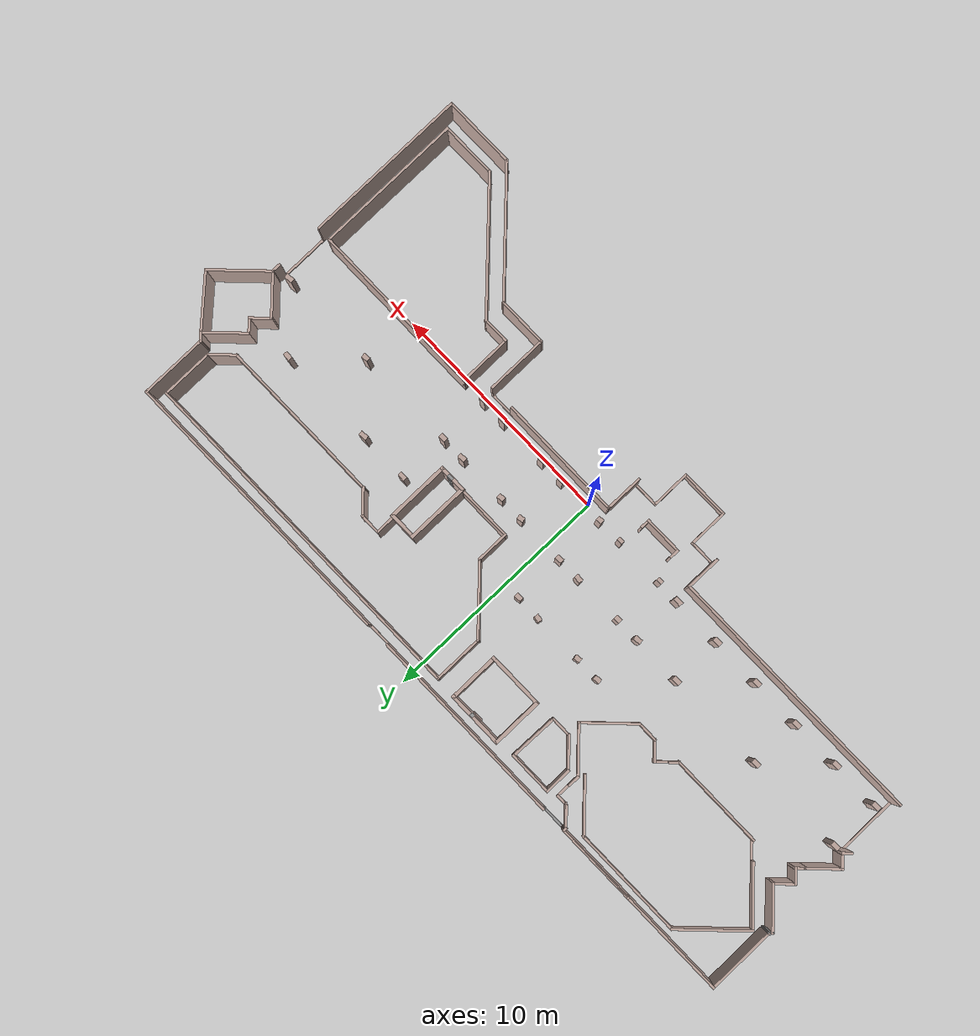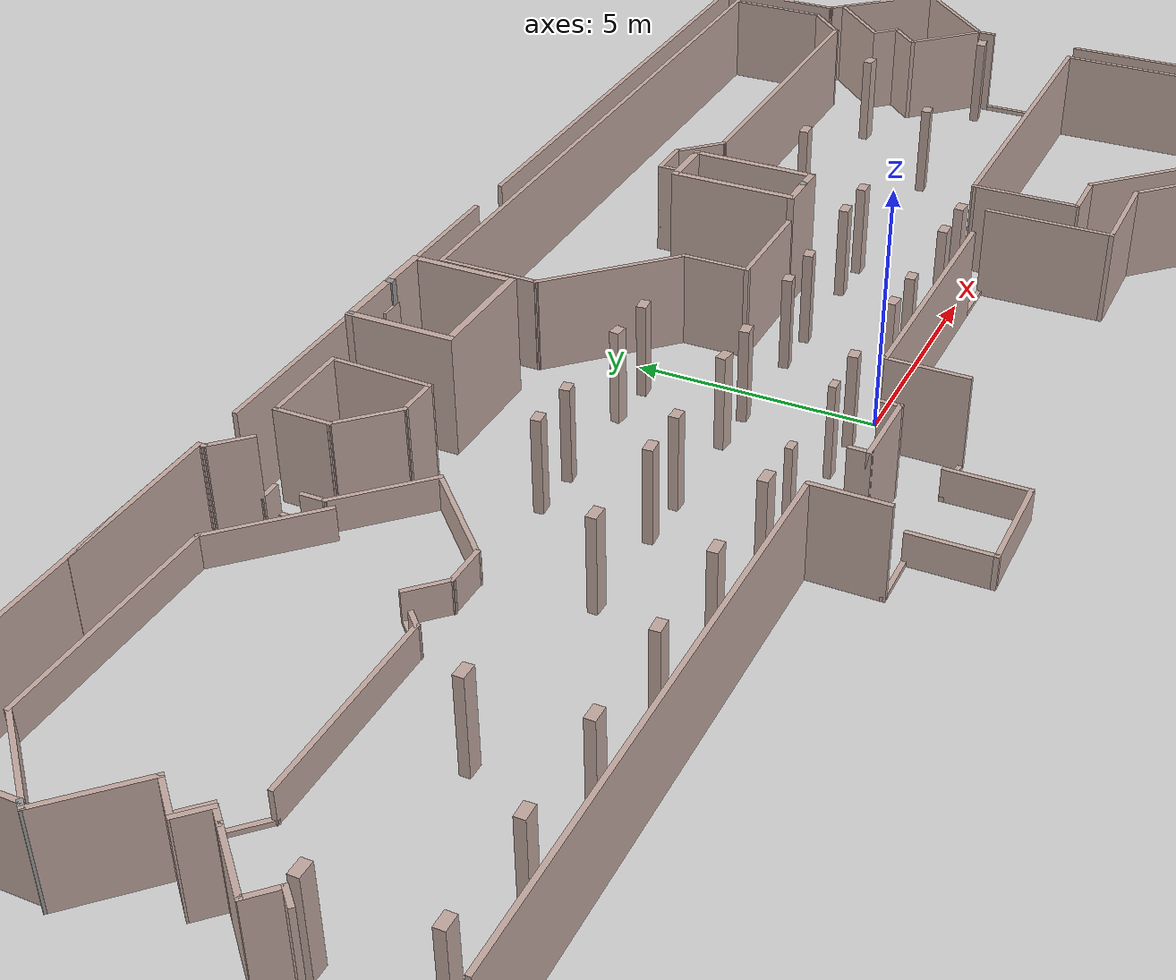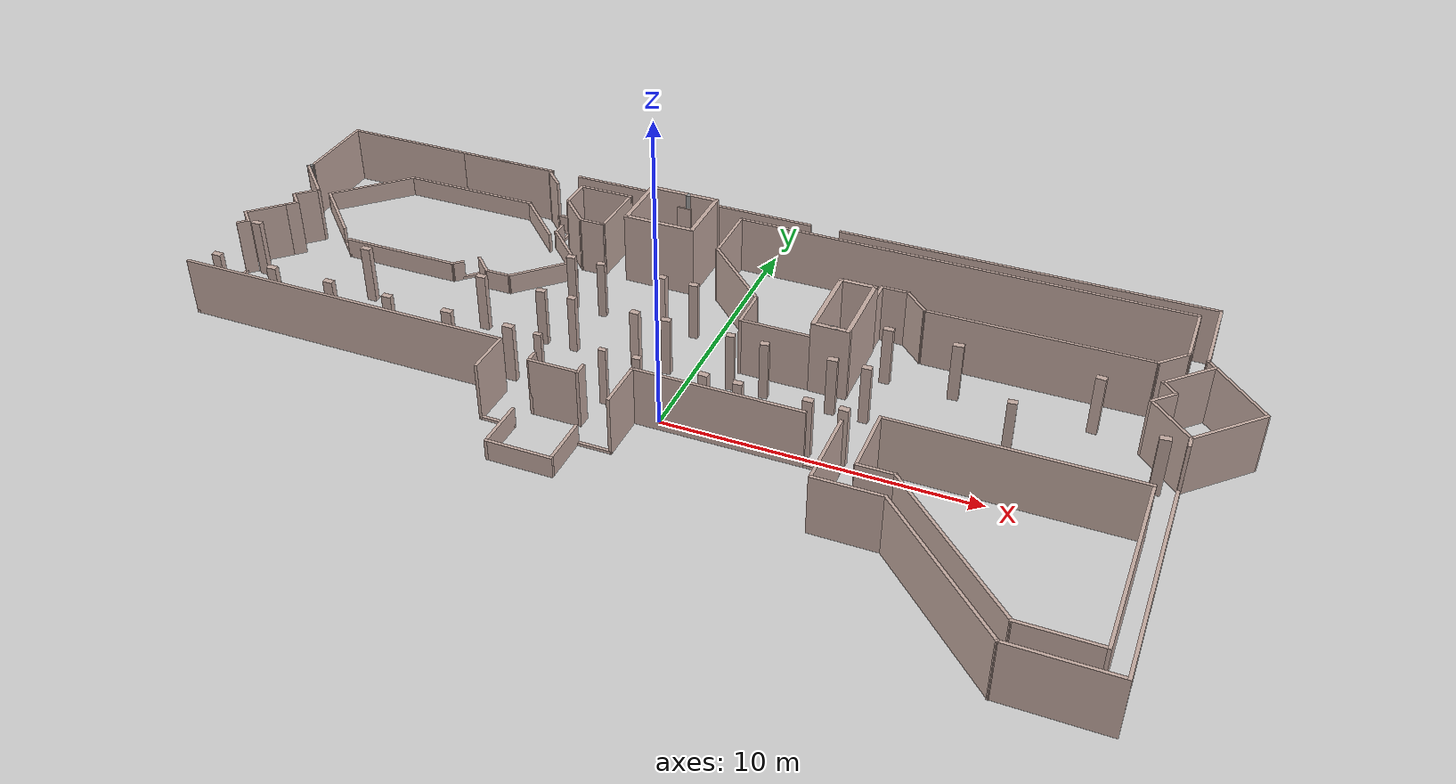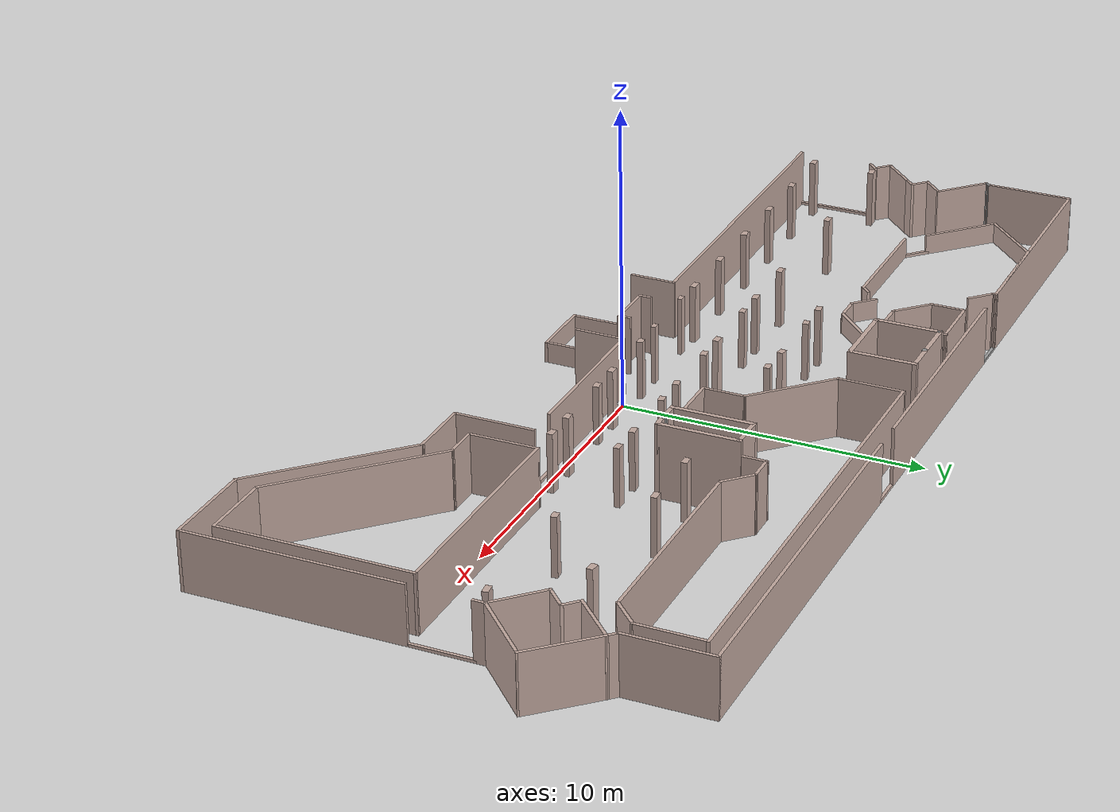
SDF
<?xml version='1.0'?>
<sdf version='1.6'>
  <model name='gedung_p'>
    <pose frame=''>0.050512 1.27019 0 0 -0 0</pose>
    <link name='Wall_104'>
      <collision name='Wall_104_Collision'>
        <geometry>
          <box>
            <size>1.44987 0.1 2</size>
          </box>
        </geometry>
        <pose frame=''>0 0 1 0 -0 0</pose>
      </collision>
      <visual name='Wall_104_Visual'>
        <pose frame=''>0 0 1 0 -0 0</pose>
        <geometry>
          <box>
            <size>1.44987 0.1 2</size>
          </box>
        </geometry>
        <material>
          <script>
            <uri>file://media/materials/scripts/gazebo.material</uri>
            <name>Gazebo/Grey</name>
          </script>
          <ambient>0.760784 0.662745 0.627451 1</ambient>
        </material>
        <meta>
          <layer>0</layer>
        </meta>
      </visual>
      <pose frame=''>-6.41651 6.00131 0 0 -0 -0.785922</pose>
    </link>
    <link name='Wall_105'>
      <collision name='Wall_105_Collision'>
        <geometry>
          <box>
            <size>0.95 0.1 2</size>
          </box>
        </geometry>
        <pose frame=''>0 0 1 0 -0 0</pose>
      </collision>
      <visual name='Wall_105_Visual'>
        <pose frame=''>0 0 1 0 -0 0</pose>
        <geometry>
          <box>
            <size>0.95 0.1 2</size>
          </box>
        </geometry>
        <material>
          <script>
            <uri>file://media/materials/scripts/gazebo.material</uri>
            <name>Gazebo/Grey</name>
          </script>
          <ambient>0.760784 0.662745 0.627451 1</ambient>
        </material>
        <meta>
          <layer>0</layer>
        </meta>
      </visual>
      <pose frame=''>-5.51451 5.52381 0 0 -0 0</pose>
    </link>
    <link name='Wall_108'>
      <collision name='Wall_108_Collision'>
        <geometry>
          <box>
            <size>2.5 0.15 2.5</size>
          </box>
        </geometry>
        <pose frame=''>0 0 1.25 0 -0 0</pose>
      </collision>
      <visual name='Wall_108_Visual'>
        <pose frame=''>0 0 1.25 0 -0 0</pose>
        <geometry>
          <box>
            <size>2.5 0.15 2.5</size>
          </box>
        </geometry>
        <material>
          <script>
            <uri>file://media/materials/scripts/gazebo.material</uri>
            <name>Gazebo/Grey</name>
          </script>
          <ambient>0.760784 0.662745 0.627451 1</ambient>
        </material>
        <meta>
          <layer>0</layer>
        </meta>
      </visual>
      <pose frame=''>-3.04751 7.6698 0 0 -0 0</pose>
    </link>
    <link name='Wall_11'>
      <collision name='Wall_11_Collision'>
        <geometry>
          <box>
            <size>1.5 0.1 2</size>
          </box>
        </geometry>
        <pose frame=''>0 0 1 0 -0 0</pose>
      </collision>
      <visual name='Wall_11_Visual'>
        <pose frame=''>0 0 1 0 -0 0</pose>
        <geometry>
          <box>
            <size>1.5 0.1 2</size>
          </box>
        </geometry>
        <material>
          <script>
            <uri>file://media/materials/scripts/gazebo.material</uri>
            <name>Gazebo/Grey</name>
          </script>
          <ambient>0.760784 0.662745 0.627451 1</ambient>
        </material>
        <meta>
          <layer>0</layer>
        </meta>
      </visual>
      <pose frame=''>-16.1925 2.05681 0 0 -0 0.785398</pose>
    </link>
    <link name='Wall_116'>
      <collision name='Wall_116_Collision'>
        <geometry>
          <box>
            <size>1.20046 0.1 0.1</size>
          </box>
        </geometry>
        <pose frame=''>0 0 0.05 0 -0 0</pose>
      </collision>
      <visual name='Wall_116_Visual'>
        <pose frame=''>0 0 0.05 0 -0 0</pose>
        <geometry>
          <box>
            <size>1.20046 0.1 0.1</size>
          </box>
        </geometry>
        <material>
          <script>
            <uri>file://media/materials/scripts/gazebo.material</uri>
            <name>Gazebo/Grey</name>
          </script>
          <ambient>1 1 1 1</ambient>
        </material>
        <meta>
          <layer>0</layer>
        </meta>
      </visual>
      <pose frame=''>-7.82151 8.1548 0 0 -0 3.14159</pose>
    </link>
    <link name='Wall_119'>
      <collision name='Wall_119_Collision'>
        <geometry>
          <box>
            <size>8.7 0.1 2</size>
          </box>
        </geometry>
        <pose frame=''>0 0 1 0 -0 0</pose>
      </collision>
      <visual name='Wall_119_Visual'>
        <pose frame=''>0 0 1 0 -0 0</pose>
        <geometry>
          <box>
            <size>8.7 0.1 2</size>
          </box>
        </geometry>
        <material>
          <script>
            <uri>file://media/materials/scripts/gazebo.material</uri>
            <name>Gazebo/Grey</name>
          </script>
          <ambient>0.760784 0.662745 0.627451 1</ambient>
        </material>
        <meta>
          <layer>0</layer>
        </meta>
      </visual>
      <pose frame=''>-2.97151 8.1548 0 0 -0 0</pose>
    </link>
    <link name='Wall_122'>
      <collision name='Wall_122_Collision'>
        <geometry>
          <box>
            <size>2.45 0.1 0.7</size>
          </box>
        </geometry>
        <pose frame=''>0 0 0.35 0 -0 0</pose>
      </collision>
      <visual name='Wall_122_Visual'>
        <pose frame=''>0 0 0.35 0 -0 0</pose>
        <geometry>
          <box>
            <size>2.45 0.1 0.7</size>
          </box>
        </geometry>
        <material>
          <script>
            <uri>file://media/materials/scripts/gazebo.material</uri>
            <name>Gazebo/Grey</name>
          </script>
          <ambient>0.760784 0.662745 0.627451 1</ambient>
        </material>
        <meta>
          <layer>0</layer>
        </meta>
      </visual>
      <pose frame=''>-8.34851 6.9748 0 0 -0 -0.785398</pose>
    </link>
    <link name='Wall_124'>
      <collision name='Wall_124_Collision'>
        <geometry>
          <box>
            <size>1.2 0.1 2</size>
          </box>
        </geometry>
        <pose frame=''>0 0 1 0 -0 0</pose>
      </collision>
      <visual name='Wall_124_Visual'>
        <pose frame=''>0 0 1 0 -0 0</pose>
        <geometry>
          <box>
            <size>1.2 0.1 2</size>
          </box>
        </geometry>
        <material>
          <script>
            <uri>file://media/materials/scripts/gazebo.material</uri>
            <name>Gazebo/Grey</name>
          </script>
          <ambient>0.760784 0.662745 0.627451 1</ambient>
        </material>
        <meta>
          <layer>0</layer>
        </meta>
      </visual>
      <pose frame=''>-6.89351 7.02881 0 0 -0 1.5708</pose>
    </link>
    <link name='Wall_125'>
      <collision name='Wall_125_Collision'>
        <geometry>
          <box>
            <size>1.95 0.1 2</size>
          </box>
        </geometry>
        <pose frame=''>0 0 1 0 -0 0</pose>
      </collision>
      <visual name='Wall_125_Visual'>
        <pose frame=''>0 0 1 0 -0 0</pose>
        <geometry>
          <box>
            <size>1.95 0.1 2</size>
          </box>
        </geometry>
        <material>
          <script>
            <uri>file://media/materials/scripts/gazebo.material</uri>
            <name>Gazebo/Grey</name>
          </script>
          <ambient>0.760784 0.662745 0.627451 1</ambient>
        </material>
        <meta>
          <layer>0</layer>
        </meta>
      </visual>
      <pose frame=''>-5.96851 7.57881 0 0 -0 0</pose>
    </link>
    <link name='Wall_126'>
      <collision name='Wall_126_Collision'>
        <geometry>
          <box>
            <size>2.15551 0.1 2</size>
          </box>
        </geometry>
        <pose frame=''>0 0 1 0 -0 0</pose>
      </collision>
      <visual name='Wall_126_Visual'>
        <pose frame=''>0 0 1 0 -0 0</pose>
        <geometry>
          <box>
            <size>2.15551 0.1 2</size>
          </box>
        </geometry>
        <material>
          <script>
            <uri>file://media/materials/scripts/gazebo.material</uri>
            <name>Gazebo/Grey</name>
          </script>
          <ambient>0.760784 0.662745 0.627451 1</ambient>
        </material>
        <meta>
          <layer>0</layer>
        </meta>
      </visual>
      <pose frame=''>-5.06651 6.55131 0 0 -0 -1.59318</pose>
    </link>
    <link name='Wall_128'>
      <collision name='Wall_128_Collision'>
        <geometry>
          <box>
            <size>2.25 0.15 2.5</size>
          </box>
        </geometry>
        <pose frame=''>0 0 1.25 0 -0 0</pose>
      </collision>
      <visual name='Wall_128_Visual'>
        <pose frame=''>0 0 1.25 0 -0 0</pose>
        <geometry>
          <box>
            <size>2.25 0.15 2.5</size>
          </box>
        </geometry>
        <material>
          <script>
            <uri>file://media/materials/scripts/gazebo.material</uri>
            <name>Gazebo/Grey</name>
          </script>
          <ambient>0.760784 0.662745 0.627451 1</ambient>
        </material>
        <meta>
          <layer>0</layer>
        </meta>
      </visual>
      <pose frame=''>-4.22251 6.61981 0 0 -0 -1.5708</pose>
    </link>
    <link name='Wall_129'>
      <collision name='Wall_129_Collision'>
        <geometry>
          <box>
            <size>2.5 0.15 2.5</size>
          </box>
        </geometry>
        <pose frame=''>0 0 1.25 0 -0 0</pose>
      </collision>
      <visual name='Wall_129_Visual'>
        <pose frame=''>0 0 1.25 0 -0 0</pose>
        <geometry>
          <box>
            <size>2.5 0.15 2.5</size>
          </box>
        </geometry>
        <material>
          <script>
            <uri>file://media/materials/scripts/gazebo.material</uri>
            <name>Gazebo/Grey</name>
          </script>
          <ambient>0.760784 0.662745 0.627451 1</ambient>
        </material>
        <meta>
          <layer>0</layer>
        </meta>
      </visual>
      <pose frame=''>-3.04751 5.5698 0 0 -0 0</pose>
    </link>
    <link name='Wall_130'>
      <collision name='Wall_130_Collision'>
        <geometry>
          <box>
            <size>2.25 0.15 2.5</size>
          </box>
        </geometry>
        <pose frame=''>0 0 1.25 0 -0 0</pose>
      </collision>
      <visual name='Wall_130_Visual'>
        <pose frame=''>0 0 1.25 0 -0 0</pose>
        <geometry>
          <box>
            <size>2.25 0.15 2.5</size>
          </box>
        </geometry>
        <material>
          <script>
            <uri>file://media/materials/scripts/gazebo.material</uri>
            <name>Gazebo/Grey</name>
          </script>
          <ambient>0.760784 0.662745 0.627451 1</ambient>
        </material>
        <meta>
          <layer>0</layer>
        </meta>
      </visual>
      <pose frame=''>-1.87251 6.61981 0 0 -0 1.5708</pose>
    </link>
    <link name='Wall_132'>
      <collision name='Wall_132_Collision'>
        <geometry>
          <box>
            <size>2.20004 0.1 2</size>
          </box>
        </geometry>
        <pose frame=''>0 0 1 0 -0 0</pose>
      </collision>
      <visual name='Wall_132_Visual'>
        <pose frame=''>0 0 1 0 -0 0</pose>
        <geometry>
          <box>
            <size>2.20004 0.1 2</size>
          </box>
        </geometry>
        <material>
          <script>
            <uri>file://media/materials/scripts/gazebo.material</uri>
            <name>Gazebo/Grey</name>
          </script>
          <ambient>0.760784 0.662745 0.627451 1</ambient>
        </material>
        <meta>
          <layer>0</layer>
        </meta>
      </visual>
      <pose frame=''>-0.943512 6.5908 0 0 -0 -1.5708</pose>
    </link>
    <link name='Wall_137'>
      <collision name='Wall_137_Collision'>
        <geometry>
          <box>
            <size>3.20031 0.1 2</size>
          </box>
        </geometry>
        <pose frame=''>0 0 1 0 -0 0</pose>
      </collision>
      <visual name='Wall_137_Visual'>
        <pose frame=''>0 0 1 0 -0 0</pose>
        <geometry>
          <box>
            <size>3.20031 0.1 2</size>
          </box>
        </geometry>
        <material>
          <script>
            <uri>file://media/materials/scripts/gazebo.material</uri>
            <name>Gazebo/Grey</name>
          </script>
          <ambient>0.760784 0.662745 0.627451 1</ambient>
        </material>
        <meta>
          <layer>0</layer>
        </meta>
      </visual>
      <pose frame=''>0.152488 4.4448 0 0 -0 -0.785398</pose>
    </link>
    <link name='Wall_138'>
      <collision name='Wall_138_Collision'>
        <geometry>
          <box>
            <size>1.45007 0.1 2</size>
          </box>
        </geometry>
        <pose frame=''>0 0 1 0 -0 0</pose>
      </collision>
      <visual name='Wall_138_Visual'>
        <pose frame=''>0 0 1 0 -0 0</pose>
        <geometry>
          <box>
            <size>1.45007 0.1 2</size>
          </box>
        </geometry>
        <material>
          <script>
            <uri>file://media/materials/scripts/gazebo.material</uri>
            <name>Gazebo/Grey</name>
          </script>
          <ambient>0.760784 0.662745 0.627451 1</ambient>
        </material>
        <meta>
          <layer>0</layer>
        </meta>
      </visual>
      <pose frame=''>1.24849 2.67381 0 0 -0 -1.5708</pose>
    </link>
    <link name='Wall_139'>
      <collision name='Wall_139_Collision'>
        <geometry>
          <box>
            <size>2.45043 0.1 2</size>
          </box>
        </geometry>
        <pose frame=''>0 0 1 0 -0 0</pose>
      </collision>
      <visual name='Wall_139_Visual'>
        <pose frame=''>0 0 1 0 -0 0</pose>
        <geometry>
          <box>
            <size>2.45043 0.1 2</size>
          </box>
        </geometry>
        <material>
          <script>
            <uri>file://media/materials/scripts/gazebo.material</uri>
            <name>Gazebo/Grey</name>
          </script>
          <ambient>0.760784 0.662745 0.627451 1</ambient>
        </material>
        <meta>
          <layer>0</layer>
        </meta>
      </visual>
      <pose frame=''>2.42349 1.9988 0 0 -0 0</pose>
    </link>
    <link name='Wall_140'>
      <collision name='Wall_140_Collision'>
        <geometry>
          <box>
            <size>2.75 0.15 2.5</size>
          </box>
        </geometry>
        <pose frame=''>0 0 1.25 0 -0 0</pose>
      </collision>
      <visual name='Wall_140_Visual'>
        <pose frame=''>0 0 1.25 0 -0 0</pose>
        <geometry>
          <box>
            <size>2.75 0.15 2.5</size>
          </box>
        </geometry>
        <material>
          <script>
            <uri>file://media/materials/scripts/gazebo.material</uri>
            <name>Gazebo/Grey</name>
          </script>
          <ambient>0.760784 0.662745 0.627451 1</ambient>
        </material>
        <meta>
          <layer>0</layer>
        </meta>
      </visual>
      <pose frame=''>3.59849 3.29881 0 0 -0 1.5708</pose>
    </link>
    <link name='Wall_141'>
      <collision name='Wall_141_Collision'>
        <geometry>
          <box>
            <size>1.25 0.15 2.5</size>
          </box>
        </geometry>
        <pose frame=''>0 0 1.25 0 -0 0</pose>
      </collision>
      <visual name='Wall_141_Visual'>
        <pose frame=''>0 0 1.25 0 -0 0</pose>
        <geometry>
          <box>
            <size>1.25 0.15 2.5</size>
          </box>
        </geometry>
        <material>
          <script>
            <uri>file://media/materials/scripts/gazebo.material</uri>
            <name>Gazebo/Grey</name>
          </script>
          <ambient>0.760784 0.662745 0.627451 1</ambient>
        </material>
        <meta>
          <layer>0</layer>
        </meta>
      </visual>
      <pose frame=''>4.14849 4.5988 0 0 -0 0</pose>
    </link>
    <link name='Wall_142'>
      <collision name='Wall_142_Collision'>
        <geometry>
          <box>
            <size>2.75 0.15 2.5</size>
          </box>
        </geometry>
        <pose frame=''>0 0 1.25 0 -0 0</pose>
      </collision>
      <visual name='Wall_142_Visual'>
        <pose frame=''>0 0 1.25 0 -0 0</pose>
        <geometry>
          <box>
            <size>2.75 0.15 2.5</size>
          </box>
        </geometry>
        <material>
          <script>
            <uri>file://media/materials/scripts/gazebo.material</uri>
            <name>Gazebo/Grey</name>
          </script>
          <ambient>0.760784 0.662745 0.627451 1</ambient>
        </material>
        <meta>
          <layer>0</layer>
        </meta>
      </visual>
      <pose frame=''>4.69849 3.29881 0 0 -0 -1.5708</pose>
    </link>
    <link name='Wall_143'>
      <collision name='Wall_143_Collision'>
        <geometry>
          <box>
            <size>1.25 0.15 2.5</size>
          </box>
        </geometry>
        <pose frame=''>0 0 1.25 0 -0 0</pose>
      </collision>
      <visual name='Wall_143_Visual'>
        <pose frame=''>0 0 1.25 0 -0 0</pose>
        <geometry>
          <box>
            <size>1.25 0.15 2.5</size>
          </box>
        </geometry>
        <material>
          <script>
            <uri>file://media/materials/scripts/gazebo.material</uri>
            <name>Gazebo/Grey</name>
          </script>
          <ambient>0.760784 0.662745 0.627451 1</ambient>
        </material>
        <meta>
          <layer>0</layer>
        </meta>
      </visual>
      <pose frame=''>4.14849 1.9988 0 0 -0 3.14159</pose>
    </link>
    <link name='Wall_145'>
      <collision name='Wall_145_Collision'>
        <geometry>
          <box>
            <size>15.25 0.1 2</size>
          </box>
        </geometry>
        <pose frame=''>0 0 1 0 -0 0</pose>
      </collision>
      <visual name='Wall_145_Visual'>
        <pose frame=''>0 0 1 0 -0 0</pose>
        <geometry>
          <box>
            <size>15.25 0.1 2</size>
          </box>
        </geometry>
        <material>
          <script>
            <uri>file://media/materials/scripts/gazebo.material</uri>
            <name>Gazebo/Grey</name>
          </script>
          <ambient>0.760784 0.662745 0.627451 1</ambient>
        </material>
        <meta>
          <layer>0</layer>
        </meta>
      </visual>
      <pose frame=''>6.63149 7.64081 0 0 -0 0</pose>
    </link>
    <link name='Wall_147'>
      <collision name='Wall_147_Collision'>
        <geometry>
          <box>
            <size>1.2 0.1 0.1</size>
          </box>
        </geometry>
        <pose frame=''>0 0 0.05 0 -0 0</pose>
      </collision>
      <visual name='Wall_147_Visual'>
        <pose frame=''>0 0 0.05 0 -0 0</pose>
        <geometry>
          <box>
            <size>1.2 0.1 0.1</size>
          </box>
        </geometry>
        <material>
          <script>
            <uri>file://media/materials/scripts/gazebo.material</uri>
            <name>Gazebo/Grey</name>
          </script>
          <ambient>0.760784 0.662745 0.627451 1</ambient>
        </material>
        <meta>
          <layer>0</layer>
        </meta>
      </visual>
      <pose frame=''>1.87849 8.1548 0 0 -0 0</pose>
    </link>
    <link name='Wall_149'>
      <collision name='Wall_149_Collision'>
        <geometry>
          <box>
            <size>0.95 0.1 2</size>
          </box>
        </geometry>
        <pose frame=''>0 0 1 0 -0 0</pose>
      </collision>
      <visual name='Wall_149_Visual'>
        <pose frame=''>0 0 1 0 -0 0</pose>
        <geometry>
          <box>
            <size>0.95 0.1 2</size>
          </box>
        </geometry>
        <material>
          <script>
            <uri>file://media/materials/scripts/gazebo.material</uri>
            <name>Gazebo/Grey</name>
          </script>
          <ambient>0.760784 0.662745 0.627451 1</ambient>
        </material>
        <meta>
          <layer>0</layer>
        </meta>
      </visual>
      <pose frame=''>4.69849 5.02381 0 0 -0 1.5708</pose>
    </link>
    <link name='Wall_150'>
      <collision name='Wall_150_Collision'>
        <geometry>
          <box>
            <size>0.95 0.1 2</size>
          </box>
        </geometry>
        <pose frame=''>0 0 1 0 -0 0</pose>
      </collision>
      <visual name='Wall_150_Visual'>
        <pose frame=''>0 0 1 0 -0 0</pose>
        <geometry>
          <box>
            <size>0.95 0.1 2</size>
          </box>
        </geometry>
        <material>
          <script>
            <uri>file://media/materials/scripts/gazebo.material</uri>
            <name>Gazebo/Grey</name>
          </script>
          <ambient>0.760784 0.662745 0.627451 1</ambient>
        </material>
        <meta>
          <layer>0</layer>
        </meta>
      </visual>
      <pose frame=''>5.12349 5.44881 0 0 -0 0</pose>
    </link>
    <link name='Wall_151'>
      <collision name='Wall_151_Collision'>
        <geometry>
          <box>
            <size>1.2 0.1 2</size>
          </box>
        </geometry>
        <pose frame=''>0 0 1 0 -0 0</pose>
      </collision>
      <visual name='Wall_151_Visual'>
        <pose frame=''>0 0 1 0 -0 0</pose>
        <geometry>
          <box>
            <size>1.2 0.1 2</size>
          </box>
        </geometry>
        <material>
          <script>
            <uri>file://media/materials/scripts/gazebo.material</uri>
            <name>Gazebo/Grey</name>
          </script>
          <ambient>0.760784 0.662745 0.627451 1</ambient>
        </material>
        <meta>
          <layer>0</layer>
        </meta>
      </visual>
      <pose frame=''>5.93749 5.0598 0 0 -0 -0.785398</pose>
    </link>
    <link name='Wall_152'>
      <collision name='Wall_152_Collision'>
        <geometry>
          <box>
            <size>7.2 0.1 2</size>
          </box>
        </geometry>
        <pose frame=''>0 0 1 0 -0 0</pose>
      </collision>
      <visual name='Wall_152_Visual'>
        <pose frame=''>0 0 1 0 -0 0</pose>
        <geometry>
          <box>
            <size>7.2 0.1 2</size>
          </box>
        </geometry>
        <material>
          <script>
            <uri>file://media/materials/scripts/gazebo.material</uri>
            <name>Gazebo/Grey</name>
          </script>
          <ambient>0.760784 0.662745 0.627451 1</ambient>
        </material>
        <meta>
          <layer>0</layer>
        </meta>
      </visual>
      <pose frame=''>9.87649 4.6708 0 0 -0 0</pose>
    </link>
    <link name='Wall_154'>
      <collision name='Wall_154_Collision'>
        <geometry>
          <box>
            <size>1.20026 0.1 2</size>
          </box>
        </geometry>
        <pose frame=''>0 0 1 0 -0 0</pose>
      </collision>
      <visual name='Wall_154_Visual'>
        <pose frame=''>0 0 1 0 -0 0</pose>
        <geometry>
          <box>
            <size>1.20026 0.1 2</size>
          </box>
        </geometry>
        <material>
          <script>
            <uri>file://media/materials/scripts/gazebo.material</uri>
            <name>Gazebo/Grey</name>
          </script>
          <ambient>0.760784 0.662745 0.627451 1</ambient>
        </material>
        <meta>
          <layer>0</layer>
        </meta>
      </visual>
      <pose frame=''>13.8155 5.0598 0 0 -0 0.785398</pose>
    </link>
    <link name='Wall_155'>
      <collision name='Wall_155_Collision'>
        <geometry>
          <box>
            <size>2.19982 0.1 2</size>
          </box>
        </geometry>
        <pose frame=''>0 0 1 0 -0 0</pose>
      </collision>
      <visual name='Wall_155_Visual'>
        <pose frame=''>0 0 1 0 -0 0</pose>
        <geometry>
          <box>
            <size>2.19982 0.1 2</size>
          </box>
        </geometry>
        <material>
          <script>
            <uri>file://media/materials/scripts/gazebo.material</uri>
            <name>Gazebo/Grey</name>
          </script>
          <ambient>0.760784 0.662745 0.627451 1</ambient>
        </material>
        <meta>
          <layer>0</layer>
        </meta>
      </visual>
      <pose frame=''>14.2045 6.4988 0 0 -0 1.5708</pose>
    </link>
    <link name='Wall_157'>
      <collision name='Wall_157_Collision'>
        <geometry>
          <box>
            <size>12.45 0.1 2</size>
          </box>
        </geometry>
        <pose frame=''>0 0 1 0 -0 0</pose>
      </collision>
      <visual name='Wall_157_Visual'>
        <pose frame=''>0 0 1 0 -0 0</pose>
        <geometry>
          <box>
            <size>12.45 0.1 2</size>
          </box>
        </geometry>
        <material>
          <script>
            <uri>file://media/materials/scripts/gazebo.material</uri>
            <name>Gazebo/Grey</name>
          </script>
          <ambient>0.760784 0.662745 0.627451 1</ambient>
        </material>
        <meta>
          <layer>0</layer>
        </meta>
      </visual>
      <pose frame=''>8.60349 8.1548 0 0 -0 0</pose>
    </link>
    <link name='Wall_159'>
      <collision name='Wall_159_Collision'>
        <geometry>
          <box>
            <size>2.95 0.1 2</size>
          </box>
        </geometry>
        <pose frame=''>0 0 1 0 -0 0</pose>
      </collision>
      <visual name='Wall_159_Visual'>
        <pose frame=''>0 0 1 0 -0 0</pose>
        <geometry>
          <box>
            <size>2.95 0.1 2</size>
          </box>
        </geometry>
        <material>
          <script>
            <uri>file://media/materials/scripts/gazebo.material</uri>
            <name>Gazebo/Grey</name>
          </script>
          <ambient>0.760784 0.662745 0.627451 1</ambient>
        </material>
        <meta>
          <layer>0</layer>
        </meta>
      </visual>
      <pose frame=''>14.7785 6.7298 0 0 -0 -1.5708</pose>
    </link>
    <link name='Wall_161'>
      <collision name='Wall_161_Collision'>
        <geometry>
          <box>
            <size>0.449311 0.1 2</size>
          </box>
        </geometry>
        <pose frame=''>0 0 1 0 -0 0</pose>
      </collision>
      <visual name='Wall_161_Visual'>
        <pose frame=''>0 0 1 0 -0 0</pose>
        <geometry>
          <box>
            <size>0.449311 0.1 2</size>
          </box>
        </geometry>
        <material>
          <script>
            <uri>file://media/materials/scripts/gazebo.material</uri>
            <name>Gazebo/Grey</name>
          </script>
          <ambient>0.760784 0.662745 0.627451 1</ambient>
        </material>
        <meta>
          <layer>0</layer>
        </meta>
      </visual>
      <pose frame=''>14.902 5.18131 0 0 -0 -0.785398</pose>
    </link>
    <link name='Wall_162'>
      <collision name='Wall_162_Collision'>
        <geometry>
          <box>
            <size>1.95 0.1 2</size>
          </box>
        </geometry>
        <pose frame=''>0 0 1 0 -0 0</pose>
      </collision>
      <visual name='Wall_162_Visual'>
        <pose frame=''>0 0 1 0 -0 0</pose>
        <geometry>
          <box>
            <size>1.95 0.1 2</size>
          </box>
        </geometry>
        <material>
          <script>
            <uri>file://media/materials/scripts/gazebo.material</uri>
            <name>Gazebo/Grey</name>
          </script>
          <ambient>0.760784 0.662745 0.627451 1</ambient>
        </material>
        <meta>
          <layer>0</layer>
        </meta>
      </visual>
      <pose frame=''>14.3715 4.4033 0 0 -0 -2.35581</pose>
    </link>
    <link name='Wall_164'>
      <collision name='Wall_164_Collision'>
        <geometry>
          <box>
            <size>0.699982 0.1 2</size>
          </box>
        </geometry>
        <pose frame=''>0 0 1 0 -0 0</pose>
      </collision>
      <visual name='Wall_164_Visual'>
        <pose frame=''>0 0 1 0 -0 0</pose>
        <geometry>
          <box>
            <size>0.699982 0.1 2</size>
          </box>
        </geometry>
        <material>
          <script>
            <uri>file://media/materials/scripts/gazebo.material</uri>
            <name>Gazebo/Grey</name>
          </script>
          <ambient>0.760784 0.662745 0.627451 1</ambient>
        </material>
        <meta>
          <layer>0</layer>
        </meta>
      </visual>
      <pose frame=''>13.93 3.53681 0 0 -0 -0.78422</pose>
    </link>
    <link name='Wall_165'>
      <collision name='Wall_165_Collision'>
        <geometry>
          <box>
            <size>0.950209 0.1 2</size>
          </box>
        </geometry>
        <pose frame=''>0 0 1 0 -0 0</pose>
      </collision>
      <visual name='Wall_165_Visual'>
        <pose frame=''>0 0 1 0 -0 0</pose>
        <geometry>
          <box>
            <size>0.950209 0.1 2</size>
          </box>
        </geometry>
        <material>
          <script>
            <uri>file://media/materials/scripts/gazebo.material</uri>
            <name>Gazebo/Grey</name>
          </script>
          <ambient>0.760784 0.662745 0.627451 1</ambient>
        </material>
        <meta>
          <layer>0</layer>
        </meta>
      </visual>
      <pose frame=''>13.842 3.02431 0 0 -0 -2.35619</pose>
    </link>
    <link name='Wall_166'>
      <collision name='Wall_166_Collision'>
        <geometry>
          <box>
            <size>1.94965 0.1 2</size>
          </box>
        </geometry>
        <pose frame=''>0 0 1 0 -0 0</pose>
      </collision>
      <visual name='Wall_166_Visual'>
        <pose frame=''>0 0 1 0 -0 0</pose>
        <geometry>
          <box>
            <size>1.94965 0.1 2</size>
          </box>
        </geometry>
        <material>
          <script>
            <uri>file://media/materials/scripts/gazebo.material</uri>
            <name>Gazebo/Grey</name>
          </script>
          <ambient>0.760784 0.662745 0.627451 1</ambient>
        </material>
        <meta>
          <layer>0</layer>
        </meta>
      </visual>
      <pose frame=''>14.1955 2.06981 0 0 -0 -0.785398</pose>
    </link>
    <link name='Wall_169'>
      <collision name='Wall_169_Collision'>
        <geometry>
          <box>
            <size>2.69932 0.1 2</size>
          </box>
        </geometry>
        <pose frame=''>0 0 1 0 -0 0</pose>
      </collision>
      <visual name='Wall_169_Visual'>
        <pose frame=''>0 0 1 0 -0 0</pose>
        <geometry>
          <box>
            <size>2.69932 0.1 2</size>
          </box>
        </geometry>
        <material>
          <script>
            <uri>file://media/materials/scripts/gazebo.material</uri>
            <name>Gazebo/Grey</name>
          </script>
          <ambient>0.760784 0.662745 0.627451 1</ambient>
        </material>
        <meta>
          <layer>0</layer>
        </meta>
      </visual>
      <pose frame=''>15.7685 2.3348 0 0 -0 0.785398</pose>
    </link>
    <link name='Wall_17'>
      <collision name='Wall_17_Collision'>
        <geometry>
          <box>
            <size>0.449929 0.1 2</size>
          </box>
        </geometry>
        <pose frame=''>0 0 1 0 -0 0</pose>
      </collision>
      <visual name='Wall_17_Visual'>
        <pose frame=''>0 0 1 0 -0 0</pose>
        <geometry>
          <box>
            <size>0.449929 0.1 2</size>
          </box>
        </geometry>
        <material>
          <script>
            <uri>file://media/materials/scripts/gazebo.material</uri>
            <name>Gazebo/Grey</name>
          </script>
          <ambient>0.760784 0.662745 0.627451 1</ambient>
        </material>
        <meta>
          <layer>0</layer>
        </meta>
      </visual>
      <pose frame=''>-15.574 2.6753 0 0 -0 0.785398</pose>
    </link>
    <link name='Wall_173'>
      <collision name='Wall_173_Collision'>
        <geometry>
          <box>
            <size>2.55273 0.1 2</size>
          </box>
        </geometry>
        <pose frame=''>0 0 1 0 -0 0</pose>
      </collision>
      <visual name='Wall_173_Visual'>
        <pose frame=''>0 0 1 0 -0 0</pose>
        <geometry>
          <box>
            <size>2.55273 0.1 2</size>
          </box>
        </geometry>
        <material>
          <script>
            <uri>file://media/materials/scripts/gazebo.material</uri>
            <name>Gazebo/Grey</name>
          </script>
          <ambient>0.760784 0.662745 0.627451 1</ambient>
        </material>
        <meta>
          <layer>0</layer>
        </meta>
      </visual>
      <pose frame=''>15.8565 4.1558 0 0 -0 -0.826345</pose>
    </link>
    <link name='Wall_175'>
      <collision name='Wall_175_Collision'>
        <geometry>
          <box>
            <size>0.45 0.1 2</size>
          </box>
        </geometry>
        <pose frame=''>0 0 1 0 -0 0</pose>
      </collision>
      <visual name='Wall_175_Visual'>
        <pose frame=''>0 0 1 0 -0 0</pose>
        <geometry>
          <box>
            <size>0.45 0.1 2</size>
          </box>
        </geometry>
        <material>
          <script>
            <uri>file://media/materials/scripts/gazebo.material</uri>
            <name>Gazebo/Grey</name>
          </script>
          <ambient>0.760784 0.662745 0.627451 1</ambient>
        </material>
        <meta>
          <layer>0</layer>
        </meta>
      </visual>
      <pose frame=''>14.8495 1.2408 0 0 -0 -1.5708</pose>
    </link>
    <link name='Wall_176'>
      <collision name='Wall_176_Collision'>
        <geometry>
          <box>
            <size>2.2 0.1 0.1</size>
          </box>
        </geometry>
        <pose frame=''>0 0 0.05 0 -0 0</pose>
      </collision>
      <visual name='Wall_176_Visual'>
        <pose frame=''>0 0 0.05 0 -0 0</pose>
        <geometry>
          <box>
            <size>2.2 0.1 0.1</size>
          </box>
        </geometry>
        <material>
          <script>
            <uri>file://media/materials/scripts/gazebo.material</uri>
            <name>Gazebo/Grey</name>
          </script>
          <ambient>0.760784 0.662745 0.627451 1</ambient>
        </material>
        <meta>
          <layer>0</layer>
        </meta>
      </visual>
      <pose frame=''>14.8495 0.015805 0 0 -0 -1.5708</pose>
    </link>
    <link name='Wall_178'>
      <collision name='Wall_178_Collision'>
        <geometry>
          <box>
            <size>7.2 0.1 2</size>
          </box>
        </geometry>
        <pose frame=''>0 0 1 0 -0 0</pose>
      </collision>
      <visual name='Wall_178_Visual'>
        <pose frame=''>0 0 1 0 -0 0</pose>
        <geometry>
          <box>
            <size>7.2 0.1 2</size>
          </box>
        </geometry>
        <material>
          <script>
            <uri>file://media/materials/scripts/gazebo.material</uri>
            <name>Gazebo/Grey</name>
          </script>
          <ambient>0.760784 0.662745 0.627451 1</ambient>
        </material>
        <meta>
          <layer>0</layer>
        </meta>
      </visual>
      <pose frame=''>14.8495 -4.5842 0 0 -0 -1.5708</pose>
    </link>
    <link name='Wall_18'>
      <collision name='Wall_18_Collision'>
        <geometry>
          <box>
            <size>0.7 0.1 2</size>
          </box>
        </geometry>
        <pose frame=''>0 0 1 0 -0 0</pose>
      </collision>
      <visual name='Wall_18_Visual'>
        <pose frame=''>0 0 1 0 -0 0</pose>
        <geometry>
          <box>
            <size>0.7 0.1 2</size>
          </box>
        </geometry>
        <material>
          <script>
            <uri>file://media/materials/scripts/gazebo.material</uri>
            <name>Gazebo/Grey</name>
          </script>
          <ambient>0.760784 0.662745 0.627451 1</ambient>
        </material>
        <meta>
          <layer>0</layer>
        </meta>
      </visual>
      <pose frame=''>-15.6625 3.01131 0 0 -0 2.35502</pose>
    </link>
    <link name='Wall_180'>
      <collision name='Wall_180_Collision'>
        <geometry>
          <box>
            <size>3.2 0.1 2</size>
          </box>
        </geometry>
        <pose frame=''>0 0 1 0 -0 0</pose>
      </collision>
      <visual name='Wall_180_Visual'>
        <pose frame=''>0 0 1 0 -0 0</pose>
        <geometry>
          <box>
            <size>3.2 0.1 2</size>
          </box>
        </geometry>
        <material>
          <script>
            <uri>file://media/materials/scripts/gazebo.material</uri>
            <name>Gazebo/Grey</name>
          </script>
          <ambient>0.760784 0.662745 0.627451 1</ambient>
        </material>
        <meta>
          <layer>0</layer>
        </meta>
      </visual>
      <pose frame=''>13.2995 -8.1342 0 0 -0 3.14159</pose>
    </link>
    <link name='Wall_181'>
      <collision name='Wall_181_Collision'>
        <geometry>
          <box>
            <size>5.7 0.1 2</size>
          </box>
        </geometry>
        <pose frame=''>0 0 1 0 -0 0</pose>
      </collision>
      <visual name='Wall_181_Visual'>
        <pose frame=''>0 0 1 0 -0 0</pose>
        <geometry>
          <box>
            <size>5.7 0.1 2</size>
          </box>
        </geometry>
        <material>
          <script>
            <uri>file://media/materials/scripts/gazebo.material</uri>
            <name>Gazebo/Grey</name>
          </script>
          <ambient>0.760784 0.662745 0.627451 1</ambient>
        </material>
        <meta>
          <layer>0</layer>
        </meta>
      </visual>
      <pose frame=''>9.76949 -6.15419 0 0 -0 2.35619</pose>
    </link>
    <link name='Wall_182'>
      <collision name='Wall_182_Collision'>
        <geometry>
          <box>
            <size>2.2 0.1 2</size>
          </box>
        </geometry>
        <pose frame=''>0 0 1 0 -0 0</pose>
      </collision>
      <visual name='Wall_182_Visual'>
        <pose frame=''>0 0 1 0 -0 0</pose>
        <geometry>
          <box>
            <size>2.2 0.1 2</size>
          </box>
        </geometry>
        <material>
          <script>
            <uri>file://media/materials/scripts/gazebo.material</uri>
            <name>Gazebo/Grey</name>
          </script>
          <ambient>0.760784 0.662745 0.627451 1</ambient>
        </material>
        <meta>
          <layer>0</layer>
        </meta>
      </visual>
      <pose frame=''>6.73949 -4.1742 0 0 -0 3.14159</pose>
    </link>
    <link name='Wall_189'>
      <collision name='Wall_189_Collision'>
        <geometry>
          <box>
            <size>2.7 0.1 2</size>
          </box>
        </geometry>
        <pose frame=''>0 0 1 0 -0 0</pose>
      </collision>
      <visual name='Wall_189_Visual'>
        <pose frame=''>0 0 1 0 -0 0</pose>
        <geometry>
          <box>
            <size>2.7 0.1 2</size>
          </box>
        </geometry>
        <material>
          <script>
            <uri>file://media/materials/scripts/gazebo.material</uri>
            <name>Gazebo/Grey</name>
          </script>
          <ambient>0.760784 0.662745 0.627451 1</ambient>
        </material>
        <meta>
          <layer>0</layer>
        </meta>
      </visual>
      <pose frame=''>5.68949 -2.87419 0 0 -0 1.5708</pose>
    </link>
    <link name='Wall_19'>
      <collision name='Wall_19_Collision'>
        <geometry>
          <box>
            <size>0.949911 0.1 2</size>
          </box>
        </geometry>
        <pose frame=''>0 0 1 0 -0 0</pose>
      </collision>
      <visual name='Wall_19_Visual'>
        <pose frame=''>0 0 1 0 -0 0</pose>
        <geometry>
          <box>
            <size>0.949911 0.1 2</size>
          </box>
        </geometry>
        <material>
          <script>
            <uri>file://media/materials/scripts/gazebo.material</uri>
            <name>Gazebo/Grey</name>
          </script>
          <ambient>0.760784 0.662745 0.627451 1</ambient>
        </material>
        <meta>
          <layer>0</layer>
        </meta>
      </visual>
      <pose frame=''>-15.574 3.52431 0 0 -0 0.785398</pose>
    </link>
    <link name='Wall_190'>
      <collision name='Wall_190_Collision'>
        <geometry>
          <box>
            <size>1.189 0.1 0.1</size>
          </box>
        </geometry>
        <pose frame=''>0 0 0.05 0 -0 0</pose>
      </collision>
      <visual name='Wall_190_Visual'>
        <pose frame=''>0 0 0.05 0 -0 0</pose>
        <geometry>
          <box>
            <size>1.189 0.1 0.1</size>
          </box>
        </geometry>
        <material>
          <script>
            <uri>file://media/materials/scripts/gazebo.material</uri>
            <name>Gazebo/Grey</name>
          </script>
          <ambient>0.760784 0.662745 0.627451 1</ambient>
        </material>
        <meta>
          <layer>0</layer>
        </meta>
      </visual>
      <pose frame=''>5.14499 -1.5742 0 0 -0 3.14159</pose>
    </link>
    <link name='Wall_191'>
      <collision name='Wall_191_Collision'>
        <geometry>
          <box>
            <size>5.44985 0.1 2</size>
          </box>
        </geometry>
        <pose frame=''>0 0 1 0 -0 0</pose>
      </collision>
      <visual name='Wall_191_Visual'>
        <pose frame=''>0 0 1 0 -0 0</pose>
        <geometry>
          <box>
            <size>5.44985 0.1 2</size>
          </box>
        </geometry>
        <material>
          <script>
            <uri>file://media/materials/scripts/gazebo.material</uri>
            <name>Gazebo/Grey</name>
          </script>
          <ambient>0.760784 0.662745 0.627451 1</ambient>
        </material>
        <meta>
          <layer>0</layer>
        </meta>
      </visual>
      <pose frame=''>1.92549 -1.5742 0 0 -0 3.14159</pose>
    </link>
    <link name='Wall_192'>
      <collision name='Wall_192_Collision'>
        <geometry>
          <box>
            <size>1.70004 0.1 2</size>
          </box>
        </geometry>
        <pose frame=''>0 0 1 0 -0 0</pose>
      </collision>
      <visual name='Wall_192_Visual'>
        <pose frame=''>0 0 1 0 -0 0</pose>
        <geometry>
          <box>
            <size>1.70004 0.1 2</size>
          </box>
        </geometry>
        <material>
          <script>
            <uri>file://media/materials/scripts/gazebo.material</uri>
            <name>Gazebo/Grey</name>
          </script>
          <ambient>0.760784 0.662745 0.627451 1</ambient>
        </material>
        <meta>
          <layer>0</layer>
        </meta>
      </visual>
      <pose frame=''>-0.755012 -2.37419 0 0 -0 -1.57767</pose>
    </link>
    <link name='Wall_194'>
      <collision name='Wall_194_Collision'>
        <geometry>
          <box>
            <size>1.2 0.1 0.1</size>
          </box>
        </geometry>
        <pose frame=''>0 0 0.05 0 -0 0</pose>
      </collision>
      <visual name='Wall_194_Visual'>
        <pose frame=''>0 0 0.05 0 -0 0</pose>
        <geometry>
          <box>
            <size>1.2 0.1 0.1</size>
          </box>
        </geometry>
        <material>
          <script>
            <uri>file://media/materials/scripts/gazebo.material</uri>
            <name>Gazebo/Grey</name>
          </script>
          <ambient>0.760784 0.662745 0.627451 1</ambient>
        </material>
        <meta>
          <layer>0</layer>
        </meta>
      </visual>
      <pose frame=''>-1.31051 -3.1742 0 0 -0 3.14159</pose>
    </link>
    <link name='Wall_195'>
      <collision name='Wall_195_Collision'>
        <geometry>
          <box>
            <size>1.7 0.1 0.7</size>
          </box>
        </geometry>
        <pose frame=''>0 0 0.35 0 -0 0</pose>
      </collision>
      <visual name='Wall_195_Visual'>
        <pose frame=''>0 0 0.35 0 -0 0</pose>
        <geometry>
          <box>
            <size>1.7 0.1 0.7</size>
          </box>
        </geometry>
        <material>
          <script>
            <uri>file://media/materials/scripts/gazebo.material</uri>
            <name>Gazebo/Grey</name>
          </script>
          <ambient>0.760784 0.662745 0.627451 1</ambient>
        </material>
        <meta>
          <layer>0</layer>
        </meta>
      </visual>
      <pose frame=''>-1.86051 -3.97419 0 0 -0 -1.5708</pose>
    </link>
    <link name='Wall_196'>
      <collision name='Wall_196_Collision'>
        <geometry>
          <box>
            <size>2.2 0.1 0.7</size>
          </box>
        </geometry>
        <pose frame=''>0 0 0.35 0 -0 0</pose>
      </collision>
      <visual name='Wall_196_Visual'>
        <pose frame=''>0 0 0.35 0 -0 0</pose>
        <geometry>
          <box>
            <size>2.2 0.1 0.7</size>
          </box>
        </geometry>
        <material>
          <script>
            <uri>file://media/materials/scripts/gazebo.material</uri>
            <name>Gazebo/Grey</name>
          </script>
          <ambient>0.760784 0.662745 0.627451 1</ambient>
        </material>
        <meta>
          <layer>0</layer>
        </meta>
      </visual>
      <pose frame=''>-2.91051 -4.77419 0 0 -0 3.14159</pose>
    </link>
    <link name='Wall_197'>
      <collision name='Wall_197_Collision'>
        <geometry>
          <box>
            <size>1.7 0.1 0.7</size>
          </box>
        </geometry>
        <pose frame=''>0 0 0.35 0 -0 0</pose>
      </collision>
      <visual name='Wall_197_Visual'>
        <pose frame=''>0 0 0.35 0 -0 0</pose>
        <geometry>
          <box>
            <size>1.7 0.1 0.7</size>
          </box>
        </geometry>
        <material>
          <script>
            <uri>file://media/materials/scripts/gazebo.material</uri>
            <name>Gazebo/Grey</name>
          </script>
          <ambient>0.760784 0.662745 0.627451 1</ambient>
        </material>
        <meta>
          <layer>0</layer>
        </meta>
      </visual>
      <pose frame=''>-3.96051 -3.97419 0 0 -0 1.5708</pose>
    </link>
    <link name='Wall_198'>
      <collision name='Wall_198_Collision'>
        <geometry>
          <box>
            <size>1.2 0.1 0.1</size>
          </box>
        </geometry>
        <pose frame=''>0 0 0.05 0 -0 0</pose>
      </collision>
      <visual name='Wall_198_Visual'>
        <pose frame=''>0 0 0.05 0 -0 0</pose>
        <geometry>
          <box>
            <size>1.2 0.1 0.1</size>
          </box>
        </geometry>
        <material>
          <script>
            <uri>file://media/materials/scripts/gazebo.material</uri>
            <name>Gazebo/Grey</name>
          </script>
          <ambient>0.760784 0.662745 0.627451 1</ambient>
        </material>
        <meta>
          <layer>0</layer>
        </meta>
      </visual>
      <pose frame=''>-4.51051 -3.1742 0 0 -0 3.14159</pose>
    </link>
    <link name='Wall_199'>
      <collision name='Wall_199_Collision'>
        <geometry>
          <box>
            <size>1.55413 0.1 2</size>
          </box>
        </geometry>
        <pose frame=''>0 0 1 0 -0 0</pose>
      </collision>
      <visual name='Wall_199_Visual'>
        <pose frame=''>0 0 1 0 -0 0</pose>
        <geometry>
          <box>
            <size>1.55413 0.1 2</size>
          </box>
        </geometry>
        <material>
          <script>
            <uri>file://media/materials/scripts/gazebo.material</uri>
            <name>Gazebo/Grey</name>
          </script>
          <ambient>0.760784 0.662745 0.627451 1</ambient>
        </material>
        <meta>
          <layer>0</layer>
        </meta>
      </visual>
      <pose frame=''>-5.05601 -2.44719 0 0 -0 1.56461</pose>
    </link>
    <link name='Wall_201'>
      <collision name='Wall_201_Collision'>
        <geometry>
          <box>
            <size>0.45 0.1 2</size>
          </box>
        </geometry>
        <pose frame=''>0 0 1 0 -0 0</pose>
      </collision>
      <visual name='Wall_201_Visual'>
        <pose frame=''>0 0 1 0 -0 0</pose>
        <geometry>
          <box>
            <size>0.45 0.1 2</size>
          </box>
        </geometry>
        <material>
          <script>
            <uri>file://media/materials/scripts/gazebo.material</uri>
            <name>Gazebo/Grey</name>
          </script>
          <ambient>0.760784 0.662745 0.627451 1</ambient>
        </material>
        <meta>
          <layer>0</layer>
        </meta>
      </visual>
      <pose frame=''>-3.75851 -2.16319 0 0 -0 -1.5708</pose>
    </link>
    <link name='Wall_202'>
      <collision name='Wall_202_Collision'>
        <geometry>
          <box>
            <size>1.7 0.1 2</size>
          </box>
        </geometry>
        <pose frame=''>0 0 1 0 -0 0</pose>
      </collision>
      <visual name='Wall_202_Visual'>
        <pose frame=''>0 0 1 0 -0 0</pose>
        <geometry>
          <box>
            <size>1.7 0.1 2</size>
          </box>
        </geometry>
        <material>
          <script>
            <uri>file://media/materials/scripts/gazebo.material</uri>
            <name>Gazebo/Grey</name>
          </script>
          <ambient>0.760784 0.662745 0.627451 1</ambient>
        </material>
        <meta>
          <layer>0</layer>
        </meta>
      </visual>
      <pose frame=''>-2.95851 -2.33819 0 0 -0 0</pose>
    </link>
    <link name='Wall_203'>
      <collision name='Wall_203_Collision'>
        <geometry>
          <box>
            <size>0.450476 0.1 2</size>
          </box>
        </geometry>
        <pose frame=''>0 0 1 0 -0 0</pose>
      </collision>
      <visual name='Wall_203_Visual'>
        <pose frame=''>0 0 1 0 -0 0</pose>
        <geometry>
          <box>
            <size>0.450476 0.1 2</size>
          </box>
        </geometry>
        <material>
          <script>
            <uri>file://media/materials/scripts/gazebo.material</uri>
            <name>Gazebo/Grey</name>
          </script>
          <ambient>0.760784 0.662745 0.627451 1</ambient>
        </material>
        <meta>
          <layer>0</layer>
        </meta>
      </visual>
      <pose frame=''>-2.15851 -2.16319 0 0 -0 1.5708</pose>
    </link>
    <link name='Wall_205'>
      <collision name='Wall_205_Collision'>
        <geometry>
          <box>
            <size>7.7003 0.1 2</size>
          </box>
        </geometry>
        <pose frame=''>0 0 1 0 -0 0</pose>
      </collision>
      <visual name='Wall_205_Visual'>
        <pose frame=''>0 0 1 0 -0 0</pose>
        <geometry>
          <box>
            <size>7.7003 0.1 2</size>
          </box>
        </geometry>
        <material>
          <script>
            <uri>file://media/materials/scripts/gazebo.material</uri>
            <name>Gazebo/Grey</name>
          </script>
          <ambient>0.760784 0.662745 0.627451 1</ambient>
        </material>
        <meta>
          <layer>0</layer>
        </meta>
      </visual>
      <pose frame=''>10.4455 -0.995195 0 0 -0 -0.002895</pose>
    </link>
    <link name='Wall_206'>
      <collision name='Wall_206_Collision'>
        <geometry>
          <box>
            <size>6.43908 0.1 2</size>
          </box>
        </geometry>
        <pose frame=''>0 0 1 0 -0 0</pose>
      </collision>
      <visual name='Wall_206_Visual'>
        <pose frame=''>0 0 1 0 -0 0</pose>
        <geometry>
          <box>
            <size>6.43908 0.1 2</size>
          </box>
        </geometry>
        <material>
          <script>
            <uri>file://media/materials/scripts/gazebo.material</uri>
            <name>Gazebo/Grey</name>
          </script>
          <ambient>0.760784 0.662745 0.627451 1</ambient>
        </material>
        <meta>
          <layer>0</layer>
        </meta>
      </visual>
      <pose frame=''>14.2455 -4.1757 0 0 -0 -1.5708</pose>
    </link>
    <link name='Wall_209'>
      <collision name='Wall_209_Collision'>
        <geometry>
          <box>
            <size>2.44973 0.1 2</size>
          </box>
        </geometry>
        <pose frame=''>0 0 1 0 -0 0</pose>
      </collision>
      <visual name='Wall_209_Visual'>
        <pose frame=''>0 0 1 0 -0 0</pose>
        <geometry>
          <box>
            <size>2.44973 0.1 2</size>
          </box>
        </geometry>
        <material>
          <script>
            <uri>file://media/materials/scripts/gazebo.material</uri>
            <name>Gazebo/Grey</name>
          </script>
          <ambient>0.760784 0.662745 0.627451 1</ambient>
        </material>
        <meta>
          <layer>0</layer>
        </meta>
      </visual>
      <pose frame=''>13.0705 -7.3452 0 0 -0 3.14159</pose>
    </link>
    <link name='Wall_21'>
      <collision name='Wall_21_Collision'>
        <geometry>
          <box>
            <size>1.95 0.1 2</size>
          </box>
        </geometry>
        <pose frame=''>0 0 1 0 -0 0</pose>
      </collision>
      <visual name='Wall_21_Visual'>
        <pose frame=''>0 0 1 0 -0 0</pose>
        <geometry>
          <box>
            <size>1.95 0.1 2</size>
          </box>
        </geometry>
        <material>
          <script>
            <uri>file://media/materials/scripts/gazebo.material</uri>
            <name>Gazebo/Grey</name>
          </script>
          <ambient>0.760784 0.662745 0.627451 1</ambient>
        </material>
        <meta>
          <layer>0</layer>
        </meta>
      </visual>
      <pose frame=''>-15.9275 4.47881 0 0 -0 2.35619</pose>
    </link>
    <link name='Wall_210'>
      <collision name='Wall_210_Collision'>
        <geometry>
          <box>
            <size>5.94975 0.1 2</size>
          </box>
        </geometry>
        <pose frame=''>0 0 1 0 -0 0</pose>
      </collision>
      <visual name='Wall_210_Visual'>
        <pose frame=''>0 0 1 0 -0 0</pose>
        <geometry>
          <box>
            <size>5.94975 0.1 2</size>
          </box>
        </geometry>
        <material>
          <script>
            <uri>file://media/materials/scripts/gazebo.material</uri>
            <name>Gazebo/Grey</name>
          </script>
          <ambient>0.760784 0.662745 0.627451 1</ambient>
        </material>
        <meta>
          <layer>0</layer>
        </meta>
      </visual>
      <pose frame=''>9.82749 -5.27719 0 0 -0 2.35619</pose>
    </link>
    <link name='Wall_211'>
      <collision name='Wall_211_Collision'>
        <geometry>
          <box>
            <size>1.2 0.1 2</size>
          </box>
        </geometry>
        <pose frame=''>0 0 1 0 -0 0</pose>
      </collision>
      <visual name='Wall_211_Visual'>
        <pose frame=''>0 0 1 0 -0 0</pose>
        <geometry>
          <box>
            <size>1.2 0.1 2</size>
          </box>
        </geometry>
        <material>
          <script>
            <uri>file://media/materials/scripts/gazebo.material</uri>
            <name>Gazebo/Grey</name>
          </script>
          <ambient>0.760784 0.662745 0.627451 1</ambient>
        </material>
        <meta>
          <layer>0</layer>
        </meta>
      </visual>
      <pose frame=''>7.20949 -3.20919 0 0 -0 3.14159</pose>
    </link>
    <link name='Wall_214'>
      <collision name='Wall_214_Collision'>
        <geometry>
          <box>
            <size>2.32454 0.1 2</size>
          </box>
        </geometry>
        <pose frame=''>0 0 1 0 -0 0</pose>
      </collision>
      <visual name='Wall_214_Visual'>
        <pose frame=''>0 0 1 0 -0 0</pose>
        <geometry>
          <box>
            <size>2.32454 0.1 2</size>
          </box>
        </geometry>
        <material>
          <script>
            <uri>file://media/materials/scripts/gazebo.material</uri>
            <name>Gazebo/Grey</name>
          </script>
          <ambient>0.760784 0.662745 0.627451 1</ambient>
        </material>
        <meta>
          <layer>0</layer>
        </meta>
      </visual>
      <pose frame=''>6.65249 -2.09669 0 0 -0 -1.5645</pose>
    </link>
    <link name='Wall_218'>
      <collision name='Wall_218_Collision'>
        <geometry>
          <box>
            <size>0.322262 0.2 2</size>
          </box>
        </geometry>
        <pose frame=''>0 0 1 0 -0 0</pose>
      </collision>
      <visual name='Wall_218_Visual'>
        <pose frame=''>0 0 1 0 -0 0</pose>
        <geometry>
          <box>
            <size>0.322262 0.2 2</size>
          </box>
        </geometry>
        <material>
          <script>
            <uri>file://media/materials/scripts/gazebo.material</uri>
            <name>Gazebo/Grey</name>
          </script>
          <ambient>0.760784 0.662745 0.627451 1</ambient>
        </material>
        <meta>
          <layer>0</layer>
        </meta>
      </visual>
      <pose frame=''>-15.9022 -1.01464 0 0 -0 0</pose>
    </link>
    <link name='Wall_22'>
      <collision name='Wall_22_Collision'>
        <geometry>
          <box>
            <size>0.246659 0.1 2</size>
          </box>
        </geometry>
        <pose frame=''>0 0 1 0 -0 0</pose>
      </collision>
      <visual name='Wall_22_Visual'>
        <pose frame=''>0 0 1 0 -0 0</pose>
        <geometry>
          <box>
            <size>0.246659 0.1 2</size>
          </box>
        </geometry>
        <material>
          <script>
            <uri>file://media/materials/scripts/gazebo.material</uri>
            <name>Gazebo/Grey</name>
          </script>
          <ambient>1 1 1 1</ambient>
        </material>
        <meta>
          <layer>0</layer>
        </meta>
      </visual>
      <pose frame=''>-16.533 5.1878 0 0 -0 0.848118</pose>
    </link>
    <link name='Wall_220'>
      <collision name='Wall_220_Collision'>
        <geometry>
          <box>
            <size>0.330965 0.2 2</size>
          </box>
        </geometry>
        <pose frame=''>0 0 1 0 -0 0</pose>
      </collision>
      <visual name='Wall_220_Visual'>
        <pose frame=''>0 0 1 0 -0 0</pose>
        <geometry>
          <box>
            <size>0.330965 0.2 2</size>
          </box>
        </geometry>
        <material>
          <script>
            <uri>file://media/materials/scripts/gazebo.material</uri>
            <name>Gazebo/Grey</name>
          </script>
          <ambient>0.760784 0.662745 0.627451 1</ambient>
        </material>
        <meta>
          <layer>0</layer>
        </meta>
      </visual>
      <pose frame=''>-13.7647 -1.01253 0 0 -0 0.032247</pose>
    </link>
    <link name='Wall_223'>
      <collision name='Wall_223_Collision'>
        <geometry>
          <box>
            <size>0.33583 0.2 2</size>
          </box>
        </geometry>
        <pose frame=''>0 0 1 0 -0 0</pose>
      </collision>
      <visual name='Wall_223_Visual'>
        <pose frame=''>0 0 1 0 -0 0</pose>
        <geometry>
          <box>
            <size>0.33583 0.2 2</size>
          </box>
        </geometry>
        <material>
          <script>
            <uri>file://media/materials/scripts/gazebo.material</uri>
            <name>Gazebo/Grey</name>
          </script>
          <ambient>0.760784 0.662745 0.627451 1</ambient>
        </material>
        <meta>
          <layer>0</layer>
        </meta>
      </visual>
      <pose frame=''>-15.9129 1.14369 0 0 -0 3.14159</pose>
    </link>
    <link name='Wall_225'>
      <collision name='Wall_225_Collision'>
        <geometry>
          <box>
            <size>0.336699 0.2 2</size>
          </box>
        </geometry>
        <pose frame=''>0 0 1 0 -0 0</pose>
      </collision>
      <visual name='Wall_225_Visual'>
        <pose frame=''>0 0 1 0 -0 0</pose>
        <geometry>
          <box>
            <size>0.336699 0.2 2</size>
          </box>
        </geometry>
        <material>
          <script>
            <uri>file://media/materials/scripts/gazebo.material</uri>
            <name>Gazebo/Grey</name>
          </script>
          <ambient>0.760784 0.662745 0.627451 1</ambient>
        </material>
        <meta>
          <layer>0</layer>
        </meta>
      </visual>
      <pose frame=''>-11.6269 -1.00331 0 0 -0 0</pose>
    </link>
    <link name='Wall_227'>
      <collision name='Wall_227_Collision'>
        <geometry>
          <box>
            <size>0.320792 0.2 2</size>
          </box>
        </geometry>
        <pose frame=''>0 0 1 0 -0 0</pose>
      </collision>
      <visual name='Wall_227_Visual'>
        <pose frame=''>0 0 1 0 -0 0</pose>
        <geometry>
          <box>
            <size>0.320792 0.2 2</size>
          </box>
        </geometry>
        <material>
          <script>
            <uri>file://media/materials/scripts/gazebo.material</uri>
            <name>Gazebo/Grey</name>
          </script>
          <ambient>0.760784 0.662745 0.627451 1</ambient>
        </material>
        <meta>
          <layer>0</layer>
        </meta>
      </visual>
      <pose frame=''>-9.46431 -1.01152 0 0 -0 0.045423</pose>
    </link>
    <link name='Wall_229'>
      <collision name='Wall_229_Collision'>
        <geometry>
          <box>
            <size>0.342272 0.2 2</size>
          </box>
        </geometry>
        <pose frame=''>0 0 1 0 -0 0</pose>
      </collision>
      <visual name='Wall_229_Visual'>
        <pose frame=''>0 0 1 0 -0 0</pose>
        <geometry>
          <box>
            <size>0.342272 0.2 2</size>
          </box>
        </geometry>
        <material>
          <script>
            <uri>file://media/materials/scripts/gazebo.material</uri>
            <name>Gazebo/Grey</name>
          </script>
          <ambient>0.760784 0.662745 0.627451 1</ambient>
        </material>
        <meta>
          <layer>0</layer>
        </meta>
      </visual>
      <pose frame=''>-7.30446 -1.02245 0 0 -0 -3.10315</pose>
    </link>
    <link name='Wall_23'>
      <collision name='Wall_23_Collision'>
        <geometry>
          <box>
            <size>3 0.1 2</size>
          </box>
        </geometry>
        <pose frame=''>0 0 1 0 -0 0</pose>
      </collision>
      <visual name='Wall_23_Visual'>
        <pose frame=''>0 0 1 0 -0 0</pose>
        <geometry>
          <box>
            <size>3 0.1 2</size>
          </box>
        </geometry>
        <material>
          <script>
            <uri>file://media/materials/scripts/gazebo.material</uri>
            <name>Gazebo/Grey</name>
          </script>
          <ambient>0.760784 0.662745 0.627451 1</ambient>
        </material>
        <meta>
          <layer>0</layer>
        </meta>
      </visual>
      <pose frame=''>-16.4845 6.6928 0 0 -0 1.5708</pose>
    </link>
    <link name='Wall_231'>
      <collision name='Wall_231_Collision'>
        <geometry>
          <box>
            <size>0.358571 0.2 2</size>
          </box>
        </geometry>
        <pose frame=''>0 0 1 0 -0 0</pose>
      </collision>
      <visual name='Wall_231_Visual'>
        <pose frame=''>0 0 1 0 -0 0</pose>
        <geometry>
          <box>
            <size>0.358571 0.2 2</size>
          </box>
        </geometry>
        <material>
          <script>
            <uri>file://media/materials/scripts/gazebo.material</uri>
            <name>Gazebo/Grey</name>
          </script>
          <ambient>0.760784 0.662745 0.627451 1</ambient>
        </material>
        <meta>
          <layer>0</layer>
        </meta>
      </visual>
      <pose frame=''>-5.16375 -1.01425 0 0 -0 3.14159</pose>
    </link>
    <link name='Wall_233'>
      <collision name='Wall_233_Collision'>
        <geometry>
          <box>
            <size>0.260396 0.2 2</size>
          </box>
        </geometry>
        <pose frame=''>0 0 1 0 -0 0</pose>
      </collision>
      <visual name='Wall_233_Visual'>
        <pose frame=''>0 0 1 0 -0 0</pose>
        <geometry>
          <box>
            <size>0.260396 0.2 2</size>
          </box>
        </geometry>
        <material>
          <script>
            <uri>file://media/materials/scripts/gazebo.material</uri>
            <name>Gazebo/Grey</name>
          </script>
          <ambient>0.760784 0.662745 0.627451 1</ambient>
        </material>
        <meta>
          <layer>0</layer>
        </meta>
      </visual>
      <pose frame=''>-0.860454 -1.01152 0 0 -0 0.09066</pose>
    </link>
    <link name='Wall_235'>
      <collision name='Wall_235_Collision'>
        <geometry>
          <box>
            <size>0.298575 0.2 2</size>
          </box>
        </geometry>
        <pose frame=''>0 0 1 0 -0 0</pose>
      </collision>
      <visual name='Wall_235_Visual'>
        <pose frame=''>0 0 1 0 -0 0</pose>
        <geometry>
          <box>
            <size>0.298575 0.2 2</size>
          </box>
        </geometry>
        <material>
          <script>
            <uri>file://media/materials/scripts/gazebo.material</uri>
            <name>Gazebo/Grey</name>
          </script>
          <ambient>0.760784 0.662745 0.627451 1</ambient>
        </material>
        <meta>
          <layer>0</layer>
        </meta>
      </visual>
      <pose frame=''>1.29119 -1.02245 0 0 -0 -0.055499</pose>
    </link>
    <link name='Wall_237'>
      <collision name='Wall_237_Collision'>
        <geometry>
          <box>
            <size>0.292956 0.2 2</size>
          </box>
        </geometry>
        <pose frame=''>0 0 1 0 -0 0</pose>
      </collision>
      <visual name='Wall_237_Visual'>
        <pose frame=''>0 0 1 0 -0 0</pose>
        <geometry>
          <box>
            <size>0.292956 0.2 2</size>
          </box>
        </geometry>
        <material>
          <script>
            <uri>file://media/materials/scripts/gazebo.material</uri>
            <name>Gazebo/Grey</name>
          </script>
          <ambient>0.760784 0.662745 0.627451 1</ambient>
        </material>
        <meta>
          <layer>0</layer>
        </meta>
      </visual>
      <pose frame=''>2.36565 -1.02792 0 0 -0 -3.08284</pose>
    </link>
    <link name='Wall_239'>
      <collision name='Wall_239_Collision'>
        <geometry>
          <box>
            <size>0.309905 0.2 2</size>
          </box>
        </geometry>
        <pose frame=''>0 0 1 0 -0 0</pose>
      </collision>
      <visual name='Wall_239_Visual'>
        <pose frame=''>0 0 1 0 -0 0</pose>
        <geometry>
          <box>
            <size>0.309905 0.2 2</size>
          </box>
        </geometry>
        <material>
          <script>
            <uri>file://media/materials/scripts/gazebo.material</uri>
            <name>Gazebo/Grey</name>
          </script>
          <ambient>0.760784 0.662745 0.627451 1</ambient>
        </material>
        <meta>
          <layer>0</layer>
        </meta>
      </visual>
      <pose frame=''>4.51183 -1.00878 0 0 -0 0</pose>
    </link>
    <link name='Wall_242'>
      <collision name='Wall_242_Collision'>
        <geometry>
          <box>
            <size>0.15 0.15 2.5</size>
          </box>
        </geometry>
        <pose frame=''>0 0 1.25 0 -0 0</pose>
      </collision>
      <visual name='Wall_242_Visual'>
        <pose frame=''>0 0 1.25 0 -0 0</pose>
        <geometry>
          <box>
            <size>0.15 0.15 2.5</size>
          </box>
        </geometry>
        <material>
          <script>
            <uri>file://media/materials/scripts/gazebo.material</uri>
            <name>Gazebo/Grey</name>
          </script>
          <ambient>1 1 1 1</ambient>
        </material>
        <meta>
          <layer>0</layer>
        </meta>
      </visual>
      <pose frame=''>4.28764 2.00954 0 0 -0 0</pose>
    </link>
    <link name='Wall_244'>
      <collision name='Wall_244_Collision'>
        <geometry>
          <box>
            <size>0.25 0.15 2.5</size>
          </box>
        </geometry>
        <pose frame=''>0 0 1.25 0 -0 0</pose>
      </collision>
      <visual name='Wall_244_Visual'>
        <pose frame=''>0 0 1.25 0 -0 0</pose>
        <geometry>
          <box>
            <size>0.25 0.15 2.5</size>
          </box>
        </geometry>
        <material>
          <script>
            <uri>file://media/materials/scripts/gazebo.material</uri>
            <name>Gazebo/Grey</name>
          </script>
          <ambient>1 1 1 1</ambient>
        </material>
        <meta>
          <layer>0</layer>
        </meta>
      </visual>
      <pose frame=''>4.23218 2.00954 0 0 -0 3.14159</pose>
    </link>
    <link name='Wall_246'>
      <collision name='Wall_246_Collision'>
        <geometry>
          <box>
            <size>0.309496 0.2 2</size>
          </box>
        </geometry>
        <pose frame=''>0 0 1 0 -0 0</pose>
      </collision>
      <visual name='Wall_246_Visual'>
        <pose frame=''>0 0 1 0 -0 0</pose>
        <geometry>
          <box>
            <size>0.309496 0.2 2</size>
          </box>
        </geometry>
        <material>
          <script>
            <uri>file://media/materials/scripts/gazebo.material</uri>
            <name>Gazebo/Grey</name>
          </script>
          <ambient>0.760784 0.662745 0.627451 1</ambient>
        </material>
        <meta>
          <layer>0</layer>
        </meta>
      </visual>
      <pose frame=''>5.59996 -1.01699 0 0 -0 -0.049958</pose>
    </link>
    <link name='Wall_248'>
      <collision name='Wall_248_Collision'>
        <geometry>
          <box>
            <size>0.344722 0.2 2</size>
          </box>
        </geometry>
        <pose frame=''>0 0 1 0 -0 0</pose>
      </collision>
      <visual name='Wall_248_Visual'>
        <pose frame=''>0 0 1 0 -0 0</pose>
        <geometry>
          <box>
            <size>0.344722 0.2 2</size>
          </box>
        </geometry>
        <material>
          <script>
            <uri>file://media/materials/scripts/gazebo.material</uri>
            <name>Gazebo/Grey</name>
          </script>
          <ambient>0.760784 0.662745 0.627451 1</ambient>
        </material>
        <meta>
          <layer>0</layer>
        </meta>
      </visual>
      <pose frame=''>14.197 1.14518 0 0 -0 0.132552</pose>
    </link>
    <link name='Wall_25'>
      <collision name='Wall_25_Collision'>
        <geometry>
          <box>
            <size>8.2039 0.1 2</size>
          </box>
        </geometry>
        <pose frame=''>0 0 1 0 -0 0</pose>
      </collision>
      <visual name='Wall_25_Visual'>
        <pose frame=''>0 0 1 0 -0 0</pose>
        <geometry>
          <box>
            <size>8.2039 0.1 2</size>
          </box>
        </geometry>
        <material>
          <script>
            <uri>file://media/materials/scripts/gazebo.material</uri>
            <name>Gazebo/Grey</name>
          </script>
          <ambient>0.760784 0.662745 0.627451 1</ambient>
        </material>
        <meta>
          <layer>0</layer>
        </meta>
      </visual>
      <pose frame=''>-12.4325 8.1463 0 0 -0 0.000864</pose>
    </link>
    <link name='Wall_250'>
      <collision name='Wall_250_Collision'>
        <geometry>
          <box>
            <size>0.286601 0.2 2</size>
          </box>
        </geometry>
        <pose frame=''>0 0 1 0 -0 0</pose>
      </collision>
      <visual name='Wall_250_Visual'>
        <pose frame=''>0 0 1 0 -0 0</pose>
        <geometry>
          <box>
            <size>0.286601 0.2 2</size>
          </box>
        </geometry>
        <material>
          <script>
            <uri>file://media/materials/scripts/gazebo.material</uri>
            <name>Gazebo/Grey</name>
          </script>
          <ambient>0.760784 0.662745 0.627451 1</ambient>
        </material>
        <meta>
          <layer>0</layer>
        </meta>
      </visual>
      <pose frame=''>9.91253 1.1404 0 0 -0 0.110657</pose>
    </link>
    <link name='Wall_252'>
      <collision name='Wall_252_Collision'>
        <geometry>
          <box>
            <size>0.305199 0.2 2</size>
          </box>
        </geometry>
        <pose frame=''>0 0 1 0 -0 0</pose>
      </collision>
      <visual name='Wall_252_Visual'>
        <pose frame=''>0 0 1 0 -0 0</pose>
        <geometry>
          <box>
            <size>0.305199 0.2 2</size>
          </box>
        </geometry>
        <material>
          <script>
            <uri>file://media/materials/scripts/gazebo.material</uri>
            <name>Gazebo/Grey</name>
          </script>
          <ambient>0.760784 0.662745 0.627451 1</ambient>
        </material>
        <meta>
          <layer>0</layer>
        </meta>
      </visual>
      <pose frame=''>5.58982 1.13562 0 0 -0 0</pose>
    </link>
    <link name='Wall_254'>
      <collision name='Wall_254_Collision'>
        <geometry>
          <box>
            <size>0.324693 0.2 2</size>
          </box>
        </geometry>
        <pose frame=''>0 0 1 0 -0 0</pose>
      </collision>
      <visual name='Wall_254_Visual'>
        <pose frame=''>0 0 1 0 -0 0</pose>
        <geometry>
          <box>
            <size>0.324693 0.2 2</size>
          </box>
        </geometry>
        <material>
          <script>
            <uri>file://media/materials/scripts/gazebo.material</uri>
            <name>Gazebo/Grey</name>
          </script>
          <ambient>0.760784 0.662745 0.627451 1</ambient>
        </material>
        <meta>
          <layer>0</layer>
        </meta>
      </visual>
      <pose frame=''>5.58982 3.28741 0 0 -0 0</pose>
    </link>
    <link name='Wall_256'>
      <collision name='Wall_256_Collision'>
        <geometry>
          <box>
            <size>0.343771 0.2 2</size>
          </box>
        </geometry>
        <pose frame=''>0 0 1 0 -0 0</pose>
      </collision>
      <visual name='Wall_256_Visual'>
        <pose frame=''>0 0 1 0 -0 0</pose>
        <geometry>
          <box>
            <size>0.343771 0.2 2</size>
          </box>
        </geometry>
        <material>
          <script>
            <uri>file://media/materials/scripts/gazebo.material</uri>
            <name>Gazebo/Grey</name>
          </script>
          <ambient>0.760784 0.662745 0.627451 1</ambient>
        </material>
        <meta>
          <layer>0</layer>
        </meta>
      </visual>
      <pose frame=''>7.7703 3.28263 0 0 -0 0.066568</pose>
    </link>
    <link name='Wall_258'>
      <collision name='Wall_258_Collision'>
        <geometry>
          <box>
            <size>0.31516 0.2 2</size>
          </box>
        </geometry>
        <pose frame=''>0 0 1 0 -0 0</pose>
      </collision>
      <visual name='Wall_258_Visual'>
        <pose frame=''>0 0 1 0 -0 0</pose>
        <geometry>
          <box>
            <size>0.31516 0.2 2</size>
          </box>
        </geometry>
        <material>
          <script>
            <uri>file://media/materials/scripts/gazebo.material</uri>
            <name>Gazebo/Grey</name>
          </script>
          <ambient>0.760784 0.662745 0.627451 1</ambient>
        </material>
        <meta>
          <layer>0</layer>
        </meta>
      </visual>
      <pose frame=''>12.0309 3.27306 0 0 -0 -0.083141</pose>
    </link>
    <link name='Wall_26'>
      <collision name='Wall_26_Collision'>
        <geometry>
          <box>
            <size>3.5939 0.1 2</size>
          </box>
        </geometry>
        <pose frame=''>0 0 1 0 -0 0</pose>
      </collision>
      <visual name='Wall_26_Visual'>
        <pose frame=''>0 0 1 0 -0 0</pose>
        <geometry>
          <box>
            <size>3.5939 0.1 2</size>
          </box>
        </geometry>
        <material>
          <script>
            <uri>file://media/materials/scripts/gazebo.material</uri>
            <name>Gazebo/Grey</name>
          </script>
          <ambient>0.760784 0.662745 0.627451 1</ambient>
        </material>
        <meta>
          <layer>0</layer>
        </meta>
      </visual>
      <pose frame=''>-10.1275 8.1463 0 0 -0 -3.13959</pose>
    </link>
    <link name='Wall_260'>
      <collision name='Wall_260_Collision'>
        <geometry>
          <box>
            <size>0.31516 0.2 2</size>
          </box>
        </geometry>
        <pose frame=''>0 0 1 0 -0 0</pose>
      </collision>
      <visual name='Wall_260_Visual'>
        <pose frame=''>0 0 1 0 -0 0</pose>
        <geometry>
          <box>
            <size>0.31516 0.2 2</size>
          </box>
        </geometry>
        <material>
          <script>
            <uri>file://media/materials/scripts/gazebo.material</uri>
            <name>Gazebo/Grey</name>
          </script>
          <ambient>0.760784 0.662745 0.627451 1</ambient>
        </material>
        <meta>
          <layer>0</layer>
        </meta>
      </visual>
      <pose frame=''>4.52349 1.1404 0 0 -0 0.083141</pose>
    </link>
    <link name='Wall_262'>
      <collision name='Wall_262_Collision'>
        <geometry>
          <box>
            <size>0.267624 0.2 2</size>
          </box>
        </geometry>
        <pose frame=''>0 0 1 0 -0 0</pose>
      </collision>
      <visual name='Wall_262_Visual'>
        <pose frame=''>0 0 1 0 -0 0</pose>
        <geometry>
          <box>
            <size>0.267624 0.2 2</size>
          </box>
        </geometry>
        <material>
          <script>
            <uri>file://media/materials/scripts/gazebo.material</uri>
            <name>Gazebo/Grey</name>
          </script>
          <ambient>0.760784 0.662745 0.627451 1</ambient>
        </material>
        <meta>
          <layer>0</layer>
        </meta>
      </visual>
      <pose frame=''>1.27667 1.13083 0 0 -0 0.141897</pose>
    </link>
    <link name='Wall_264'>
      <collision name='Wall_264_Collision'>
        <geometry>
          <box>
            <size>0.277104 0.2 2</size>
          </box>
        </geometry>
        <pose frame=''>0 0 1 0 -0 0</pose>
      </collision>
      <visual name='Wall_264_Visual'>
        <pose frame=''>0 0 1 0 -0 0</pose>
        <geometry>
          <box>
            <size>0.277104 0.2 2</size>
          </box>
        </geometry>
        <material>
          <script>
            <uri>file://media/materials/scripts/gazebo.material</uri>
            <name>Gazebo/Grey</name>
          </script>
          <ambient>0.760784 0.662745 0.627451 1</ambient>
        </material>
        <meta>
          <layer>0</layer>
        </meta>
      </visual>
      <pose frame=''>2.38126 1.12127 0 0 -0 0.124355</pose>
    </link>
    <link name='Wall_266'>
      <collision name='Wall_266_Collision'>
        <geometry>
          <box>
            <size>0.33423 0.2 2</size>
          </box>
        </geometry>
        <pose frame=''>0 0 1 0 -0 0</pose>
      </collision>
      <visual name='Wall_266_Visual'>
        <pose frame=''>0 0 1 0 -0 0</pose>
        <geometry>
          <box>
            <size>0.33423 0.2 2</size>
          </box>
        </geometry>
        <material>
          <script>
            <uri>file://media/materials/scripts/gazebo.material</uri>
            <name>Gazebo/Grey</name>
          </script>
          <ambient>0.760784 0.662745 0.627451 1</ambient>
        </material>
        <meta>
          <layer>0</layer>
        </meta>
      </visual>
      <pose frame=''>-11.6102 1.14518 0 0 -0 0</pose>
    </link>
    <link name='Wall_268'>
      <collision name='Wall_268_Collision'>
        <geometry>
          <box>
            <size>0.333889 0.2 2</size>
          </box>
        </geometry>
        <pose frame=''>0 0 1 0 -0 0</pose>
      </collision>
      <visual name='Wall_268_Visual'>
        <pose frame=''>0 0 1 0 -0 0</pose>
        <geometry>
          <box>
            <size>0.333889 0.2 2</size>
          </box>
        </geometry>
        <material>
          <script>
            <uri>file://media/materials/scripts/gazebo.material</uri>
            <name>Gazebo/Grey</name>
          </script>
          <ambient>0.760784 0.662745 0.627451 1</ambient>
        </material>
        <meta>
          <layer>0</layer>
        </meta>
      </visual>
      <pose frame=''>-7.29702 1.12605 0 0 -0 3.14159</pose>
    </link>
    <link name='Wall_270'>
      <collision name='Wall_270_Collision'>
        <geometry>
          <box>
            <size>0.31516 0.2 2</size>
          </box>
        </geometry>
        <pose frame=''>0 0 1 0 -0 0</pose>
      </collision>
      <visual name='Wall_270_Visual'>
        <pose frame=''>0 0 1 0 -0 0</pose>
        <geometry>
          <box>
            <size>0.31516 0.2 2</size>
          </box>
        </geometry>
        <material>
          <script>
            <uri>file://media/materials/scripts/gazebo.material</uri>
            <name>Gazebo/Grey</name>
          </script>
          <ambient>0.760784 0.662745 0.627451 1</ambient>
        </material>
        <meta>
          <layer>0</layer>
        </meta>
      </visual>
      <pose frame=''>-5.1548 1.12127 0 0 -0 0.083141</pose>
    </link>
    <link name='Wall_272'>
      <collision name='Wall_272_Collision'>
        <geometry>
          <box>
            <size>0.266945 0.2 2</size>
          </box>
        </geometry>
        <pose frame=''>0 0 1 0 -0 0</pose>
      </collision>
      <visual name='Wall_272_Visual'>
        <pose frame=''>0 0 1 0 -0 0</pose>
        <geometry>
          <box>
            <size>0.266945 0.2 2</size>
          </box>
        </geometry>
        <material>
          <script>
            <uri>file://media/materials/scripts/gazebo.material</uri>
            <name>Gazebo/Grey</name>
          </script>
          <ambient>0.760784 0.662745 0.627451 1</ambient>
        </material>
        <meta>
          <layer>0</layer>
        </meta>
      </visual>
      <pose frame=''>-4.06934 1.12605 0 0 -0 0</pose>
    </link>
    <link name='Wall_274'>
      <collision name='Wall_274_Collision'>
        <geometry>
          <box>
            <size>0.286601 0.2 2</size>
          </box>
        </geometry>
        <pose frame=''>0 0 1 0 -0 0</pose>
      </collision>
      <visual name='Wall_274_Visual'>
        <pose frame=''>0 0 1 0 -0 0</pose>
        <geometry>
          <box>
            <size>0.286601 0.2 2</size>
          </box>
        </geometry>
        <material>
          <script>
            <uri>file://media/materials/scripts/gazebo.material</uri>
            <name>Gazebo/Grey</name>
          </script>
          <ambient>0.760784 0.662745 0.627451 1</ambient>
        </material>
        <meta>
          <layer>0</layer>
        </meta>
      </visual>
      <pose frame=''>-5.16914 3.28263 0 0 -0 0.110657</pose>
    </link>
    <link name='Wall_276'>
      <collision name='Wall_276_Collision'>
        <geometry>
          <box>
            <size>0.267624 0.2 2</size>
          </box>
        </geometry>
        <pose frame=''>0 0 1 0 -0 0</pose>
      </collision>
      <visual name='Wall_276_Visual'>
        <pose frame=''>0 0 1 0 -0 0</pose>
        <geometry>
          <box>
            <size>0.267624 0.2 2</size>
          </box>
        </geometry>
        <material>
          <script>
            <uri>file://media/materials/scripts/gazebo.material</uri>
            <name>Gazebo/Grey</name>
          </script>
          <ambient>0.760784 0.662745 0.627451 1</ambient>
        </material>
        <meta>
          <layer>0</layer>
        </meta>
      </visual>
      <pose frame=''>-4.08846 3.27306 0 0 -0 0.141897</pose>
    </link>
    <link name='Wall_278'>
      <collision name='Wall_278_Collision'>
        <geometry>
          <box>
            <size>0.5 0.2 2</size>
          </box>
        </geometry>
        <pose frame=''>0 0 1 0 -0 0</pose>
      </collision>
      <visual name='Wall_278_Visual'>
        <pose frame=''>0 0 1 0 -0 0</pose>
        <geometry>
          <box>
            <size>0.5 0.2 2</size>
          </box>
        </geometry>
        <material>
          <script>
            <uri>file://media/materials/scripts/gazebo.material</uri>
            <name>Gazebo/Grey</name>
          </script>
          <ambient>0.760784 0.662745 0.627451 1</ambient>
        </material>
        <meta>
          <layer>0</layer>
        </meta>
      </visual>
      <pose frame=''>-3.00554 7.6387 0 0 -0 0</pose>
    </link>
    <link name='Wall_279'>
      <collision name='Wall_279_Collision'>
        <geometry>
          <box>
            <size>0.15 0.15 2.5</size>
          </box>
        </geometry>
        <pose frame=''>0 0 1.25 0 -0 0</pose>
      </collision>
      <visual name='Wall_279_Visual'>
        <pose frame=''>0 0 1.25 0 -0 0</pose>
        <geometry>
          <box>
            <size>0.15 0.15 2.5</size>
          </box>
        </geometry>
        <material>
          <script>
            <uri>file://media/materials/scripts/gazebo.material</uri>
            <name>Gazebo/Grey</name>
          </script>
          <ambient>1 1 1 1</ambient>
        </material>
        <meta>
          <layer>0</layer>
        </meta>
      </visual>
      <pose frame=''>-2.85554 7.6387 0 0 -0 0</pose>
    </link>
    <link name='Wall_28'>
      <collision name='Wall_28_Collision'>
        <geometry>
          <box>
            <size>0.207387 0.1 2</size>
          </box>
        </geometry>
        <pose frame=''>0 0 1 0 -0 0</pose>
      </collision>
      <visual name='Wall_28_Visual'>
        <pose frame=''>0 0 1 0 -0 0</pose>
        <geometry>
          <box>
            <size>0.207387 0.1 2</size>
          </box>
        </geometry>
        <material>
          <script>
            <uri>file://media/materials/scripts/gazebo.material</uri>
            <name>Gazebo/Grey</name>
          </script>
          <ambient>0.760784 0.662745 0.627451 1</ambient>
        </material>
        <meta>
          <layer>0</layer>
        </meta>
      </visual>
      <pose frame=''>-8.38251 8.0963 0 0 -0 -1.60816</pose>
    </link>
    <link name='Wall_281'>
      <collision name='Wall_281_Collision'>
        <geometry>
          <box>
            <size>0.267624 0.2 2</size>
          </box>
        </geometry>
        <pose frame=''>0 0 1 0 -0 0</pose>
      </collision>
      <visual name='Wall_281_Visual'>
        <pose frame=''>0 0 1 0 -0 0</pose>
        <geometry>
          <box>
            <size>0.267624 0.2 2</size>
          </box>
        </geometry>
        <material>
          <script>
            <uri>file://media/materials/scripts/gazebo.material</uri>
            <name>Gazebo/Grey</name>
          </script>
          <ambient>0.760784 0.662745 0.627451 1</ambient>
        </material>
        <meta>
          <layer>0</layer>
        </meta>
      </visual>
      <pose frame=''>-1.92711 3.30175 0 0 -0 -0.141897</pose>
    </link>
    <link name='Wall_283'>
      <collision name='Wall_283_Collision'>
        <geometry>
          <box>
            <size>0.305633 0.2 2</size>
          </box>
        </geometry>
        <pose frame=''>0 0 1 0 -0 0</pose>
      </collision>
      <visual name='Wall_283_Visual'>
        <pose frame=''>0 0 1 0 -0 0</pose>
        <geometry>
          <box>
            <size>0.305633 0.2 2</size>
          </box>
        </geometry>
        <material>
          <script>
            <uri>file://media/materials/scripts/gazebo.material</uri>
            <name>Gazebo/Grey</name>
          </script>
          <ambient>0.760784 0.662745 0.627451 1</ambient>
        </material>
        <meta>
          <layer>0</layer>
        </meta>
      </visual>
      <pose frame=''>-1.90798 1.1404 0 0 -0 -0.09066</pose>
    </link>
    <link name='Wall_285'>
      <collision name='Wall_285_Collision'>
        <geometry>
          <box>
            <size>0.25 0.15 2</size>
          </box>
        </geometry>
        <pose frame=''>0 0 1 0 -0 0</pose>
      </collision>
      <visual name='Wall_285_Visual'>
        <pose frame=''>0 0 1 0 -0 0</pose>
        <geometry>
          <box>
            <size>0.25 0.15 2</size>
          </box>
        </geometry>
        <material>
          <script>
            <uri>file://media/materials/scripts/gazebo.material</uri>
            <name>Gazebo/Grey</name>
          </script>
          <ambient>0.760784 0.662745 0.627451 1</ambient>
        </material>
        <meta>
          <layer>0</layer>
        </meta>
      </visual>
      <pose frame=''>-4.12951 -1.05419 0 0 -0 0</pose>
    </link>
    <link name='Wall_287'>
      <collision name='Wall_287_Collision'>
        <geometry>
          <box>
            <size>0.25 0.15 2</size>
          </box>
        </geometry>
        <pose frame=''>0 0 1 0 -0 0</pose>
      </collision>
      <visual name='Wall_287_Visual'>
        <pose frame=''>0 0 1 0 -0 0</pose>
        <geometry>
          <box>
            <size>0.25 0.15 2</size>
          </box>
        </geometry>
        <material>
          <script>
            <uri>file://media/materials/scripts/gazebo.material</uri>
            <name>Gazebo/Grey</name>
          </script>
          <ambient>0.760784 0.662745 0.627451 1</ambient>
        </material>
        <meta>
          <layer>0</layer>
        </meta>
      </visual>
      <pose frame=''>-1.97751 -1.0352 0 0 -0 0</pose>
    </link>
    <link name='Wall_289'>
      <collision name='Wall_289_Collision'>
        <geometry>
          <box>
            <size>0.296112 0.2 2</size>
          </box>
        </geometry>
        <pose frame=''>0 0 1 0 -0 0</pose>
      </collision>
      <visual name='Wall_289_Visual'>
        <pose frame=''>0 0 1 0 -0 0</pose>
        <geometry>
          <box>
            <size>0.296112 0.2 2</size>
          </box>
        </geometry>
        <material>
          <script>
            <uri>file://media/materials/scripts/gazebo.material</uri>
            <name>Gazebo/Grey</name>
          </script>
          <ambient>0.760784 0.662745 0.627451 1</ambient>
        </material>
        <meta>
          <layer>0</layer>
        </meta>
      </visual>
      <pose frame=''>-0.841647 3.27306 0 0 -0 0.099669</pose>
    </link>
    <link name='Wall_29'>
      <collision name='Wall_29_Collision'>
        <geometry>
          <box>
            <size>0.95 0.1 2</size>
          </box>
        </geometry>
        <pose frame=''>0 0 1 0 -0 0</pose>
      </collision>
      <visual name='Wall_29_Visual'>
        <pose frame=''>0 0 1 0 -0 0</pose>
        <geometry>
          <box>
            <size>0.95 0.1 2</size>
          </box>
        </geometry>
        <material>
          <script>
            <uri>file://media/materials/scripts/gazebo.material</uri>
            <name>Gazebo/Grey</name>
          </script>
          <ambient>0.760784 0.662745 0.627451 1</ambient>
        </material>
        <meta>
          <layer>0</layer>
        </meta>
      </visual>
      <pose frame=''>-8.08401 7.7423 0 0 -0 -0.785398</pose>
    </link>
    <link name='Wall_291'>
      <collision name='Wall_291_Collision'>
        <geometry>
          <box>
            <size>0.296112 0.2 2</size>
          </box>
        </geometry>
        <pose frame=''>0 0 1 0 -0 0</pose>
      </collision>
      <visual name='Wall_291_Visual'>
        <pose frame=''>0 0 1 0 -0 0</pose>
        <geometry>
          <box>
            <size>0.296112 0.2 2</size>
          </box>
        </geometry>
        <material>
          <script>
            <uri>file://media/materials/scripts/gazebo.material</uri>
            <name>Gazebo/Grey</name>
          </script>
          <ambient>0.760784 0.662745 0.627451 1</ambient>
        </material>
        <meta>
          <layer>0</layer>
        </meta>
      </visual>
      <pose frame=''>-0.860774 1.1404 0 0 -0 0.099669</pose>
    </link>
    <link name='Wall_30'>
      <collision name='Wall_30_Collision'>
        <geometry>
          <box>
            <size>0.5 0.1 0.7</size>
          </box>
        </geometry>
        <pose frame=''>0 0 0.35 0 -0 0</pose>
      </collision>
      <visual name='Wall_30_Visual'>
        <pose frame=''>0 0 0.35 0 -0 0</pose>
        <geometry>
          <box>
            <size>0.5 0.1 0.7</size>
          </box>
        </geometry>
        <material>
          <script>
            <uri>file://media/materials/scripts/gazebo.material</uri>
            <name>Gazebo/Grey</name>
          </script>
          <ambient>0.760784 0.662745 0.627451 1</ambient>
        </material>
        <meta>
          <layer>0</layer>
        </meta>
      </visual>
      <pose frame=''>-7.58351 7.4418 0 0 -0 0</pose>
    </link>
    <link name='Wall_36'>
      <collision name='Wall_36_Collision'>
        <geometry>
          <box>
            <size>2.2 0.1 0.7</size>
          </box>
        </geometry>
        <pose frame=''>0 0 0.35 0 -0 0</pose>
      </collision>
      <visual name='Wall_36_Visual'>
        <pose frame=''>0 0 0.35 0 -0 0</pose>
        <geometry>
          <box>
            <size>2.2 0.1 0.7</size>
          </box>
        </geometry>
        <material>
          <script>
            <uri>file://media/materials/scripts/gazebo.material</uri>
            <name>Gazebo/Grey</name>
          </script>
          <ambient>0.760784 0.662745 0.627451 1</ambient>
        </material>
        <meta>
          <layer>0</layer>
        </meta>
      </visual>
      <pose frame=''>-6.64101 5.64931 0 0 -0 -0.785398</pose>
    </link>
    <link name='Wall_38'>
      <collision name='Wall_38_Collision'>
        <geometry>
          <box>
            <size>2.45 0.1 0.7</size>
          </box>
        </geometry>
        <pose frame=''>0 0 0.35 0 -0 0</pose>
      </collision>
      <visual name='Wall_38_Visual'>
        <pose frame=''>0 0 0.35 0 -0 0</pose>
        <geometry>
          <box>
            <size>2.45 0.1 0.7</size>
          </box>
        </geometry>
        <material>
          <script>
            <uri>file://media/materials/scripts/gazebo.material</uri>
            <name>Gazebo/Grey</name>
          </script>
          <ambient>0.760784 0.662745 0.627451 1</ambient>
        </material>
        <meta>
          <layer>0</layer>
        </meta>
      </visual>
      <pose frame=''>-6.72951 4.0758 0 0 -0 -2.35619</pose>
    </link>
    <link name='Wall_39'>
      <collision name='Wall_39_Collision'>
        <geometry>
          <box>
            <size>0.949701 0.1 0.7</size>
          </box>
        </geometry>
        <pose frame=''>0 0 0.35 0 -0 0</pose>
      </collision>
      <visual name='Wall_39_Visual'>
        <pose frame=''>0 0 0.35 0 -0 0</pose>
        <geometry>
          <box>
            <size>0.949701 0.1 0.7</size>
          </box>
        </geometry>
        <material>
          <script>
            <uri>file://media/materials/scripts/gazebo.material</uri>
            <name>Gazebo/Grey</name>
          </script>
          <ambient>0.760784 0.662745 0.627451 1</ambient>
        </material>
        <meta>
          <layer>0</layer>
        </meta>
      </visual>
      <pose frame=''>-7.98551 3.2448 0 0 -0 3.14159</pose>
    </link>
    <link name='Wall_40'>
      <collision name='Wall_40_Collision'>
        <geometry>
          <box>
            <size>0.949942 0.1 0.7</size>
          </box>
        </geometry>
        <pose frame=''>0 0 0.35 0 -0 0</pose>
      </collision>
      <visual name='Wall_40_Visual'>
        <pose frame=''>0 0 0.35 0 -0 0</pose>
        <geometry>
          <box>
            <size>0.949942 0.1 0.7</size>
          </box>
        </geometry>
        <material>
          <script>
            <uri>file://media/materials/scripts/gazebo.material</uri>
            <name>Gazebo/Grey</name>
          </script>
          <ambient>0.760784 0.662745 0.627451 1</ambient>
        </material>
        <meta>
          <layer>0</layer>
        </meta>
      </visual>
      <pose frame=''>-8.71101 3.5453 0 0 -0 2.35619</pose>
    </link>
    <link name='Wall_42'>
      <collision name='Wall_42_Collision'>
        <geometry>
          <box>
            <size>0.699577 0.1 0.1</size>
          </box>
        </geometry>
        <pose frame=''>0 0 0.05 0 -0 0</pose>
      </collision>
      <visual name='Wall_42_Visual'>
        <pose frame=''>0 0 0.05 0 -0 0</pose>
        <geometry>
          <box>
            <size>0.699577 0.1 0.1</size>
          </box>
        </geometry>
        <material>
          <script>
            <uri>file://media/materials/scripts/gazebo.material</uri>
            <name>Gazebo/Grey</name>
          </script>
          <ambient>0.760784 0.662745 0.627451 1</ambient>
        </material>
        <meta>
          <layer>0</layer>
        </meta>
      </visual>
      <pose frame=''>-9.22351 3.63381 0 0 -0 -2.35619</pose>
    </link>
    <link name='Wall_45'>
      <collision name='Wall_45_Collision'>
        <geometry>
          <box>
            <size>0.449951 0.1 0.7</size>
          </box>
        </geometry>
        <pose frame=''>0 0 0.35 0 -0 0</pose>
      </collision>
      <visual name='Wall_45_Visual'>
        <pose frame=''>0 0 0.35 0 -0 0</pose>
        <geometry>
          <box>
            <size>0.449951 0.1 0.7</size>
          </box>
        </geometry>
        <material>
          <script>
            <uri>file://media/materials/scripts/gazebo.material</uri>
            <name>Gazebo/Grey</name>
          </script>
          <ambient>0.760784 0.662745 0.627451 1</ambient>
        </material>
        <meta>
          <layer>0</layer>
        </meta>
      </visual>
      <pose frame=''>-9.55901 3.29831 0 0 -0 -2.35619</pose>
    </link>
    <link name='Wall_46'>
      <collision name='Wall_46_Collision'>
        <geometry>
          <box>
            <size>4.2 0.1 0.7</size>
          </box>
        </geometry>
        <pose frame=''>0 0 0.35 0 -0 0</pose>
      </collision>
      <visual name='Wall_46_Visual'>
        <pose frame=''>0 0 0.35 0 -0 0</pose>
        <geometry>
          <box>
            <size>4.2 0.1 0.7</size>
          </box>
        </geometry>
        <material>
          <script>
            <uri>file://media/materials/scripts/gazebo.material</uri>
            <name>Gazebo/Grey</name>
          </script>
          <ambient>0.760784 0.662745 0.627451 1</ambient>
        </material>
        <meta>
          <layer>0</layer>
        </meta>
      </visual>
      <pose frame=''>-11.7325 3.17481 0 0 -0 3.14159</pose>
    </link>
    <link name='Wall_48'>
      <collision name='Wall_48_Collision'>
        <geometry>
          <box>
            <size>0.55301 0.1 0.7</size>
          </box>
        </geometry>
        <pose frame=''>0 0 0.35 0 -0 0</pose>
      </collision>
      <visual name='Wall_48_Visual'>
        <pose frame=''>0 0 0.35 0 -0 0</pose>
        <geometry>
          <box>
            <size>0.55301 0.1 0.7</size>
          </box>
        </geometry>
        <material>
          <script>
            <uri>file://media/materials/scripts/gazebo.material</uri>
            <name>Gazebo/Grey</name>
          </script>
          <ambient>0.760784 0.662745 0.627451 1</ambient>
        </material>
        <meta>
          <layer>0</layer>
        </meta>
      </visual>
      <pose frame=''>-7.38501 6.61831 0 0 -0 -1.56417</pose>
    </link>
    <link name='Wall_5'>
      <collision name='Wall_5_Collision'>
        <geometry>
          <box>
            <size>2.7 0.1 0.1</size>
          </box>
        </geometry>
        <pose frame=''>0 0 0.05 0 -0 0</pose>
      </collision>
      <visual name='Wall_5_Visual'>
        <pose frame=''>0 0 0.05 0 -0 0</pose>
        <geometry>
          <box>
            <size>2.7 0.1 0.1</size>
          </box>
        </geometry>
        <material>
          <script>
            <uri>file://media/materials/scripts/gazebo.material</uri>
            <name>Gazebo/Grey</name>
          </script>
          <ambient>0.760784 0.662745 0.627451 1</ambient>
        </material>
        <meta>
          <layer>0</layer>
        </meta>
      </visual>
      <pose frame=''>-16.5105 -0.410195 0 0 -0 -1.5708</pose>
    </link>
    <link name='Wall_52'>
      <collision name='Wall_52_Collision'>
        <geometry>
          <box>
            <size>0.697008 0.1 0.1</size>
          </box>
        </geometry>
        <pose frame=''>0 0 0.05 0 -0 0</pose>
      </collision>
      <visual name='Wall_52_Visual'>
        <pose frame=''>0 0 0.05 0 -0 0</pose>
        <geometry>
          <box>
            <size>0.697008 0.1 0.1</size>
          </box>
        </geometry>
        <material>
          <script>
            <uri>file://media/materials/scripts/gazebo.material</uri>
            <name>Gazebo/Grey</name>
          </script>
          <ambient>0.760784 0.662745 0.627451 1</ambient>
        </material>
        <meta>
          <layer>0</layer>
        </meta>
      </visual>
      <pose frame=''>-7.38501 7.1433 0 0 -0 1.56577</pose>
    </link>
    <link name='Wall_54'>
      <collision name='Wall_54_Collision'>
        <geometry>
          <box>
            <size>0.95 0.1 0.1</size>
          </box>
        </geometry>
        <pose frame=''>0 0 0.05 0 -0 0</pose>
      </collision>
      <visual name='Wall_54_Visual'>
        <pose frame=''>0 0 0.05 0 -0 0</pose>
        <geometry>
          <box>
            <size>0.95 0.1 0.1</size>
          </box>
        </geometry>
        <material>
          <script>
            <uri>file://media/materials/scripts/gazebo.material</uri>
            <name>Gazebo/Grey</name>
          </script>
          <ambient>0.760784 0.662745 0.627451 1</ambient>
        </material>
        <meta>
          <layer>0</layer>
        </meta>
      </visual>
      <pose frame=''>-14.083 3.47531 0 0 -0 2.35619</pose>
    </link>
    <link name='Wall_55'>
      <collision name='Wall_55_Collision'>
        <geometry>
          <box>
            <size>2.7 0.1 0.7</size>
          </box>
        </geometry>
        <pose frame=''>0 0 0.35 0 -0 0</pose>
      </collision>
      <visual name='Wall_55_Visual'>
        <pose frame=''>0 0 0.35 0 -0 0</pose>
        <geometry>
          <box>
            <size>2.7 0.1 0.7</size>
          </box>
        </geometry>
        <material>
          <script>
            <uri>file://media/materials/scripts/gazebo.material</uri>
            <name>Gazebo/Grey</name>
          </script>
          <ambient>0.760784 0.662745 0.627451 1</ambient>
        </material>
        <meta>
          <layer>0</layer>
        </meta>
      </visual>
      <pose frame=''>-15.3025 4.6948 0 0 -0 2.35619</pose>
    </link>
    <link name='Wall_6'>
      <collision name='Wall_6_Collision'>
        <geometry>
          <box>
            <size>11.5 0.1 2</size>
          </box>
        </geometry>
        <pose frame=''>0 0 1 0 -0 0</pose>
      </collision>
      <visual name='Wall_6_Visual'>
        <pose frame=''>0 0 1 0 -0 0</pose>
        <geometry>
          <box>
            <size>11.5 0.1 2</size>
          </box>
        </geometry>
        <material>
          <script>
            <uri>file://media/materials/scripts/gazebo.material</uri>
            <name>Gazebo/Grey</name>
          </script>
          <ambient>0.760784 0.662745 0.627451 1</ambient>
        </material>
        <meta>
          <layer>0</layer>
        </meta>
      </visual>
      <pose frame=''>-10.8105 -1.71019 0 0 -0 0</pose>
    </link>
    <link name='Wall_8'>
      <collision name='Wall_8_Collision'>
        <geometry>
          <box>
            <size>0.45 0.1 2</size>
          </box>
        </geometry>
        <pose frame=''>0 0 1 0 -0 0</pose>
      </collision>
      <visual name='Wall_8_Visual'>
        <pose frame=''>0 0 1 0 -0 0</pose>
        <geometry>
          <box>
            <size>0.45 0.1 2</size>
          </box>
        </geometry>
        <material>
          <script>
            <uri>file://media/materials/scripts/gazebo.material</uri>
            <name>Gazebo/Grey</name>
          </script>
          <ambient>0.760784 0.662745 0.627451 1</ambient>
        </material>
        <meta>
          <layer>0</layer>
        </meta>
      </visual>
      <pose frame=''>-16.387 1.0133 0 0 -0 0.785398</pose>
    </link>
    <link name='Wall_84'>
      <collision name='Wall_84_Collision'>
        <geometry>
          <box>
            <size>3.2 0.1 0.7</size>
          </box>
        </geometry>
        <pose frame=''>0 0 0.35 0 -0 0</pose>
      </collision>
      <visual name='Wall_84_Visual'>
        <pose frame=''>0 0 0.35 0 -0 0</pose>
        <geometry>
          <box>
            <size>3.2 0.1 0.7</size>
          </box>
        </geometry>
        <material>
          <script>
            <uri>file://media/materials/scripts/gazebo.material</uri>
            <name>Gazebo/Grey</name>
          </script>
          <ambient>0.760784 0.662745 0.627451 1</ambient>
        </material>
        <meta>
          <layer>0</layer>
        </meta>
      </visual>
      <pose frame=''>-15.1255 6.70981 0 0 -0 0.785398</pose>
    </link>
    <link name='Wall_86'>
      <collision name='Wall_86_Collision'>
        <geometry>
          <box>
            <size>4.95 0.1 0.7</size>
          </box>
        </geometry>
        <pose frame=''>0 0 0.35 0 -0 0</pose>
      </collision>
      <visual name='Wall_86_Visual'>
        <pose frame=''>0 0 0.35 0 -0 0</pose>
        <geometry>
          <box>
            <size>4.95 0.1 0.7</size>
          </box>
        </geometry>
        <material>
          <script>
            <uri>file://media/materials/scripts/gazebo.material</uri>
            <name>Gazebo/Grey</name>
          </script>
          <ambient>0.760784 0.662745 0.627451 1</ambient>
        </material>
        <meta>
          <layer>0</layer>
        </meta>
      </visual>
      <pose frame=''>-11.6045 7.80581 0 0 -0 0</pose>
    </link>
    <link name='Wall_89'>
      <collision name='Wall_89_Collision'>
        <geometry>
          <box>
            <size>0.15 0.15 2.5</size>
          </box>
        </geometry>
        <pose frame=''>0 0 1.25 0 -0 0</pose>
      </collision>
      <visual name='Wall_89_Visual'>
        <pose frame=''>0 0 1.25 0 -0 0</pose>
        <geometry>
          <box>
            <size>0.15 0.15 2.5</size>
          </box>
        </geometry>
        <material>
          <script>
            <uri>file://media/materials/scripts/gazebo.material</uri>
            <name>Gazebo/Grey</name>
          </script>
          <ambient>1 1 1 1</ambient>
        </material>
        <meta>
          <layer>0</layer>
        </meta>
      </visual>
      <pose frame=''>-4.22251 7.6698 0 0 -0 0</pose>
    </link>
    <link name='Wall_9'>
      <collision name='Wall_9_Collision'>
        <geometry>
          <box>
            <size>0.7 0.1 2</size>
          </box>
        </geometry>
        <pose frame=''>0 0 1 0 -0 0</pose>
      </collision>
      <visual name='Wall_9_Visual'>
        <pose frame=''>0 0 1 0 -0 0</pose>
        <geometry>
          <box>
            <size>0.7 0.1 2</size>
          </box>
        </geometry>
        <material>
          <script>
            <uri>file://media/materials/scripts/gazebo.material</uri>
            <name>Gazebo/Grey</name>
          </script>
          <ambient>0.760784 0.662745 0.627451 1</ambient>
        </material>
        <meta>
          <layer>0</layer>
        </meta>
      </visual>
      <pose frame=''>-16.4755 1.3493 0 0 -0 2.35502</pose>
    </link>
    <link name='Wall_96'>
      <collision name='Wall_96_Collision'>
        <geometry>
          <box>
            <size>0.15 0.15 2.5</size>
          </box>
        </geometry>
        <pose frame=''>0 0 1.25 0 -0 0</pose>
      </collision>
      <visual name='Wall_96_Visual'>
        <pose frame=''>0 0 1.25 0 -0 0</pose>
        <geometry>
          <box>
            <size>0.15 0.15 2.5</size>
          </box>
        </geometry>
        <material>
          <script>
            <uri>file://media/materials/scripts/gazebo.material</uri>
            <name>Gazebo/Grey</name>
          </script>
          <ambient>1 1 1 1</ambient>
        </material>
        <meta>
          <layer>0</layer>
        </meta>
      </visual>
      <pose frame=''>-4.22251 7.6698 0 0 -0 0</pose>
    </link>
    <static>1</static>
  </model>
</sdf>
